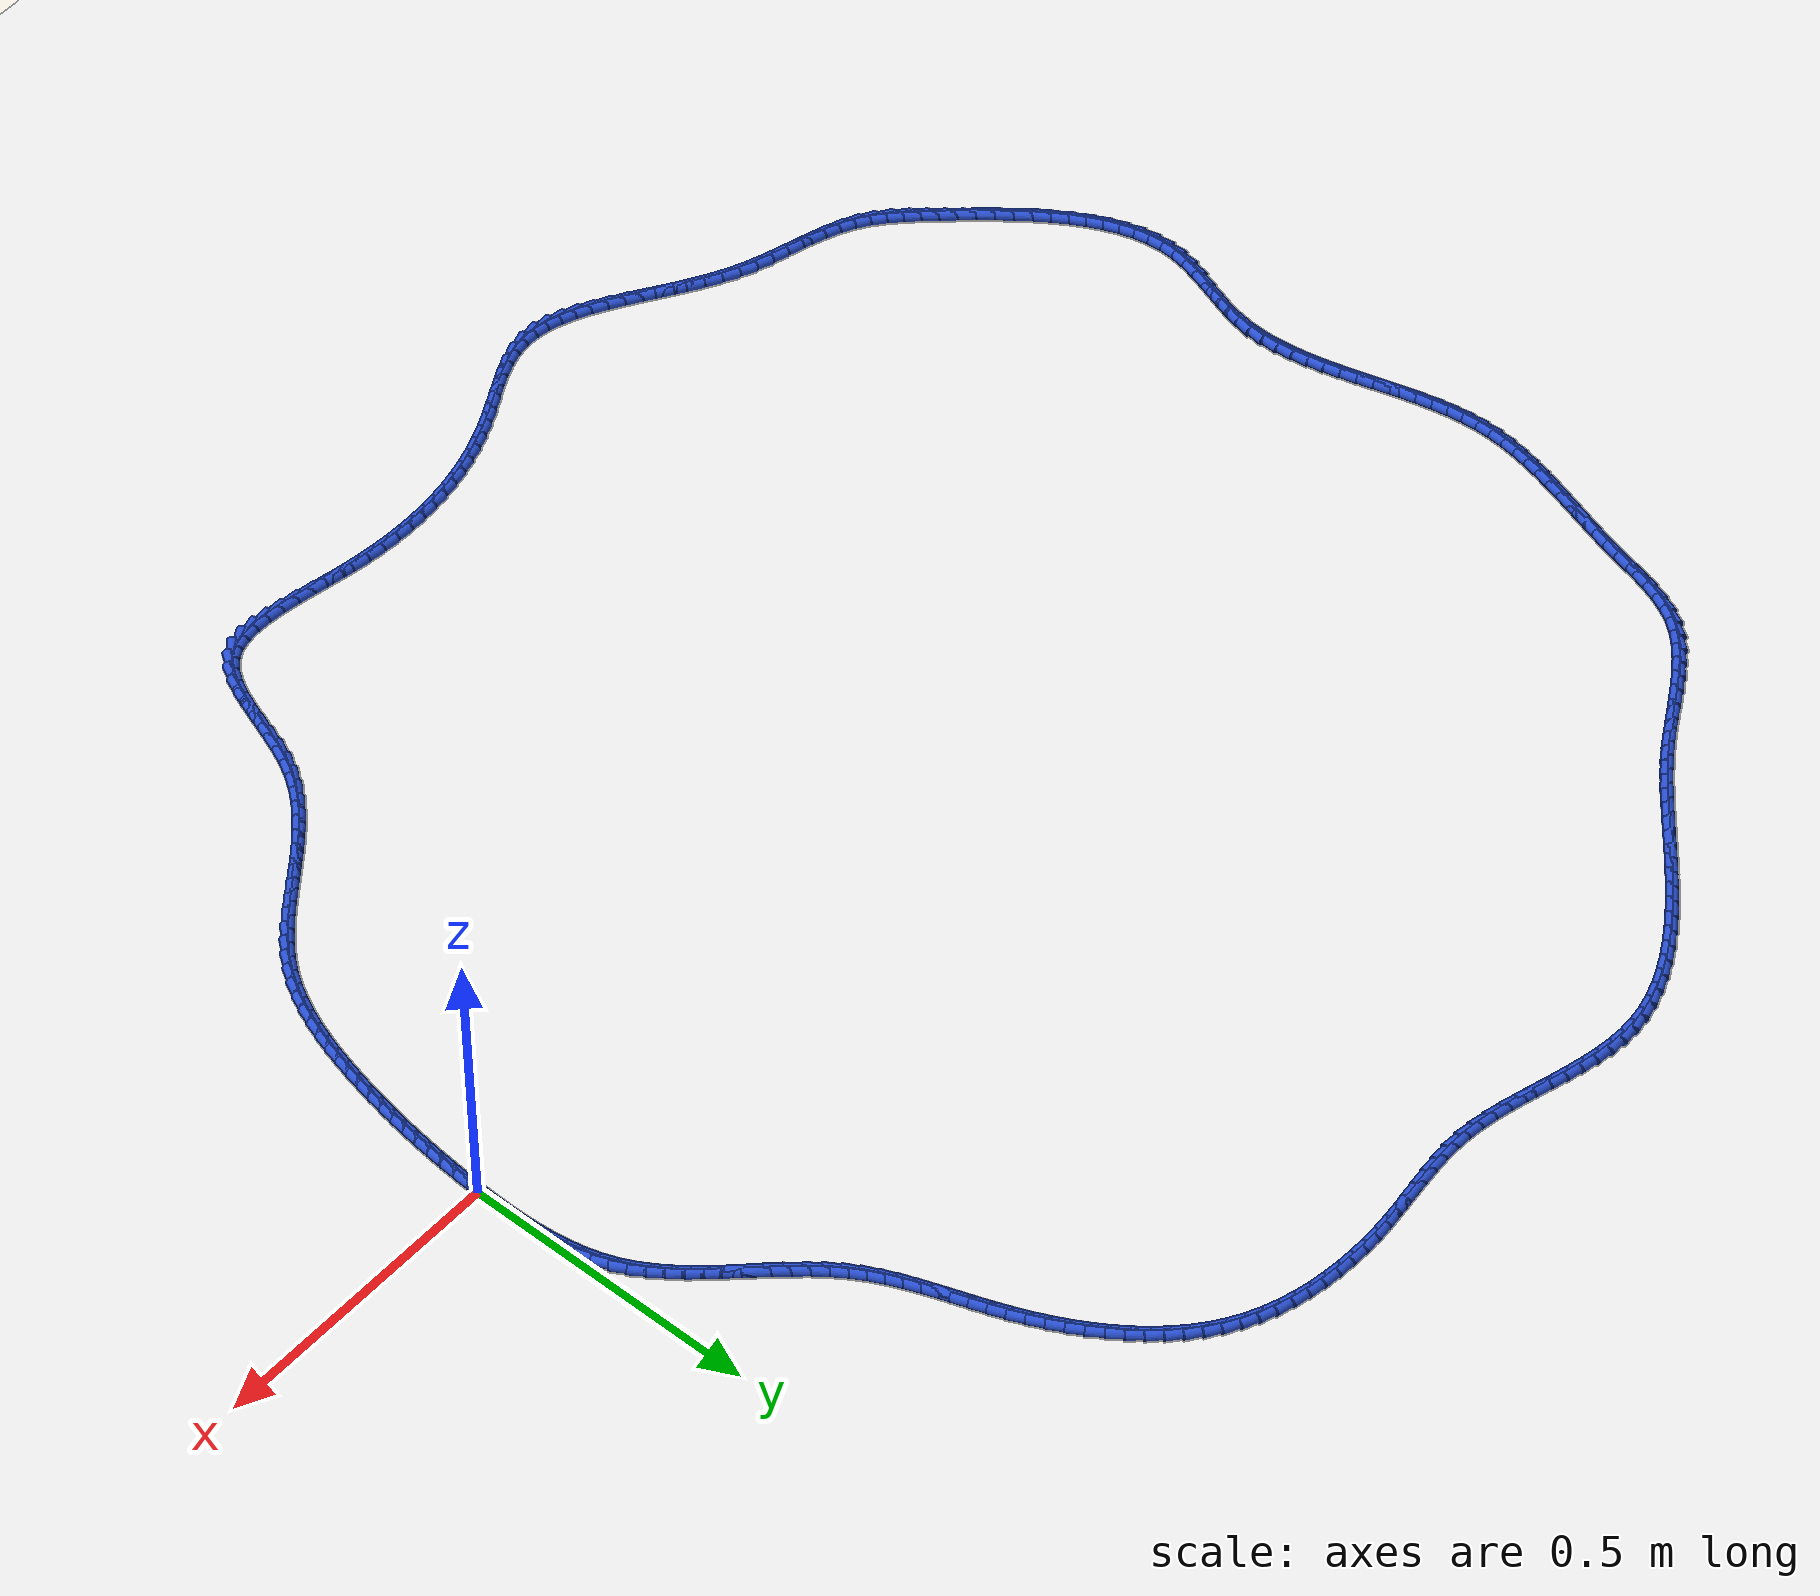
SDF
<sdf version="1.6">
 <world name="default">
  <light name="sun" type="directional">
   <pose>0 0 10 0 -0 0</pose>
   <diffuse>0.8 0.8 0.8 1</diffuse>
   <specular>0.2 0.2 0.2 1</specular>
   <attenuation>
    <range>1000</range>
    <constant>0.9</constant>
    <linear>0.01</linear>
    <quadratic>0.001</quadratic>
   </attenuation>
   <direction>-0.5 0.1 -0.9</direction>
  </light>
  <model name="ground_plane">
   <static>1</static>
   <link name="link">
    <collision name="collision">
     <geometry><plane><normal>0 0 1</normal><size>100 100</size></plane></geometry>
     <surface><friction><ode><mu>100</mu><mu2>50</mu2></ode></friction></surface>
    </collision>
    <visual name="visual">
     <cast_shadows>0</cast_shadows>
     <geometry><plane><normal>0 0 1</normal><size>100 100</size></plane></geometry>
     <material>
      <script><uri>file://media/materials/scripts/gazebo.material</uri><name>Gazebo/WhiteGlow</name></script>
     </material>
    </visual>
   </link>
  </model>
  <gravity>0 0 -9.8</gravity>
  <magnetic_field>6e-06 2.3e-05 -4.2e-05</magnetic_field>
  <atmosphere type="adiabatic"/>
  <physics name="default_physics" default="0" type="ode">
   <max_step_size>0.001</max_step_size>
   <real_time_factor>1</real_time_factor>
   <real_time_update_rate>1000</real_time_update_rate>
  </physics>
  <scene><ambient>0.4 0.4 0.4 1</ambient><background>0.7 0.7 0.7 1</background><shadows>1</shadows></scene>
  <spherical_coordinates>
   <surface_model>EARTH_WGS84</surface_model>
   <latitude_deg>0</latitude_deg>
   <longitude_deg>0</longitude_deg>
   <elevation>0</elevation>
   <heading_deg>0</heading_deg>
  </spherical_coordinates>
  <model name="line">
   <link name="link_0">
    <pose>5.44811591673966e-18 -4.85722573273506e-17 0.01 0 1.57 1.52936281463359</pose>
    <collision name="collision">
     <geometry><cylinder><radius>0.01</radius><length>0.08</length></cylinder></geometry>
    </collision>
    <visual name="visual">
     <material>
      <script><name>Gazebo/Blue</name><uri>file://media/materials/scripts/gazebo.material</uri></script>
     </material>
     <geometry><cylinder><radius>0.01</radius><length>0.08</length></cylinder></geometry>
    </visual>
   </link>
   <link name="link_1">
    <pose>0.0011541633781692302 0.02783985179669101 0.01 0 1.57 1.5510333189672778</pose>
    <collision name="collision">
     <geometry><cylinder><radius>0.01</radius><length>0.08</length></cylinder></geometry>
    </collision>
    <visual name="visual">
     <material>
      <script><name>Gazebo/Blue</name><uri>file://media/materials/scripts/gazebo.material</uri></script>
     </material>
     <geometry><cylinder><radius>0.01</radius><length>0.08</length></cylinder></geometry>
    </visual>
   </link>
   <link name="link_2">
    <pose>0.0017077863925077724 0.05584929954443413 0.01 0 1.57 -1.5615755259988313</pose>
    <collision name="collision">
     <geometry><cylinder><radius>0.01</radius><length>0.08</length></cylinder></geometry>
    </collision>
    <visual name="visual">
     <material>
      <script><name>Gazebo/Blue</name><uri>file://media/materials/scripts/gazebo.material</uri></script>
     </material>
     <geometry><cylinder><radius>0.01</radius><length>0.08</length></cylinder></geometry>
    </visual>
   </link>
   <link name="link_3">
    <pose>0.0014494072117952558 0.08386984392518775 0.01 0 1.57 -1.5248402342841438</pose>
    <collision name="collision">
     <geometry><cylinder><radius>0.01</radius><length>0.08</length></cylinder></geometry>
    </collision>
    <visual name="visual">
     <material>
      <script><name>Gazebo/Blue</name><uri>file://media/materials/scripts/gazebo.material</uri></script>
     </material>
     <geometry><cylinder><radius>0.01</radius><length>0.08</length></cylinder></geometry>
    </visual>
   </link>
   <link name="link_4">
    <pose>0.00016756400481130742 0.11174298562091044 0.01 0 1.57 -1.4797530624721642</pose>
    <collision name="collision">
     <geometry><cylinder><radius>0.01</radius><length>0.08</length></cylinder></geometry>
    </collision>
    <visual name="visual">
     <material>
      <script><name>Gazebo/Blue</name><uri>file://media/materials/scripts/gazebo.material</uri></script>
     </material>
     <geometry><cylinder><radius>0.01</radius><length>0.08</length></cylinder></geometry>
    </visual>
   </link>
   <link name="link_5">
    <pose>-0.0023492050596644453 0.13931022531356066 0.01 0 1.57 -1.425598742480633</pose>
    <collision name="collision">
     <geometry><cylinder><radius>0.01</radius><length>0.08</length></cylinder></geometry>
    </collision>
    <visual name="visual">
     <material>
      <script><name>Gazebo/Blue</name><uri>file://media/materials/scripts/gazebo.material</uri></script>
     </material>
     <geometry><cylinder><radius>0.01</radius><length>0.08</length></cylinder></geometry>
    </visual>
   </link>
   <link name="link_6">
    <pose>-0.006312361812852373 0.16641306368509692 0.01 0 1.57 -1.361627035891638</pose>
    <collision name="collision">
     <geometry><cylinder><radius>0.01</radius><length>0.08</length></cylinder></geometry>
    </collision>
    <visual name="visual">
     <material>
      <script><name>Gazebo/Blue</name><uri>file://media/materials/scripts/gazebo.material</uri></script>
     </material>
     <geometry><cylinder><radius>0.01</radius><length>0.08</length></cylinder></geometry>
    </visual>
   </link>
   <link name="link_7">
    <pose>-0.011933368085972852 0.1928930014174778 0.01 0 1.57 -1.2871847369622496</pose>
    <collision name="collision">
     <geometry><cylinder><radius>0.01</radius><length>0.08</length></cylinder></geometry>
    </collision>
    <visual name="visual">
     <material>
      <script><name>Gazebo/Blue</name><uri>file://media/materials/scripts/gazebo.material</uri></script>
     </material>
     <geometry><cylinder><radius>0.01</radius><length>0.08</length></cylinder></geometry>
    </visual>
   </link>
   <link name="link_8">
    <pose>-0.01942368571024626 0.21859153919266186 0.01 0 1.57 -1.2019158198015052</pose>
    <collision name="collision">
     <geometry><cylinder><radius>0.01</radius><length>0.08</length></cylinder></geometry>
    </collision>
    <visual name="visual">
     <material>
      <script><name>Gazebo/Blue</name><uri>file://media/materials/scripts/gazebo.material</uri></script>
     </material>
     <geometry><cylinder><radius>0.01</radius><length>0.08</length></cylinder></geometry>
    </visual>
   </link>
   <link name="link_9">
    <pose>-0.028994776516892966 0.2433501776926075 0.01 0 1.57 -1.107951390770927</pose>
    <collision name="collision">
     <geometry><cylinder><radius>0.01</radius><length>0.08</length></cylinder></geometry>
    </collision>
    <visual name="visual">
     <material>
      <script><name>Gazebo/Blue</name><uri>file://media/materials/scripts/gazebo.material</uri></script>
     </material>
     <geometry><cylinder><radius>0.01</radius><length>0.08</length></cylinder></geometry>
    </visual>
   </link>
   <link name="link_10">
    <pose>-0.04081411634225851 0.2670363689495163 0.01 0 1.57 -1.0215255866779043</pose>
    <collision name="collision">
     <geometry><cylinder><radius>0.01</radius><length>0.08</length></cylinder></geometry>
    </collision>
    <visual name="visual">
     <material>
      <script><name>Gazebo/Blue</name><uri>file://media/materials/scripts/gazebo.material</uri></script>
     </material>
     <geometry><cylinder><radius>0.01</radius><length>0.08</length></cylinder></geometry>
    </visual>
   </link>
   <link name="link_11">
    <pose>-0.054700741327095063 0.2897231413524448 0.01 0 1.57 -0.9507243869292543</pose>
    <collision name="collision">
     <geometry><cylinder><radius>0.01</radius><length>0.08</length></cylinder></geometry>
    </collision>
    <visual name="visual">
     <material>
      <script><name>Gazebo/Blue</name><uri>file://media/materials/scripts/gazebo.material</uri></script>
     </material>
     <geometry><cylinder><radius>0.01</radius><length>0.08</length></cylinder></geometry>
    </visual>
   </link>
   <link name="link_12">
    <pose>-0.07030788435505346 0.31158134575436575 0.01 0 1.57 -0.8955087621850788</pose>
    <collision name="collision">
     <geometry><cylinder><radius>0.01</radius><length>0.08</length></cylinder></geometry>
    </collision>
    <visual name="visual">
     <material>
      <script><name>Gazebo/Blue</name><uri>file://media/materials/scripts/gazebo.material</uri></script>
     </material>
     <geometry><cylinder><radius>0.01</radius><length>0.08</length></cylinder></geometry>
    </visual>
   </link>
   <link name="link_13">
    <pose>-0.08728776614763331 0.33278243017502257 0.01 0 1.57 -0.855288107946799</pose>
    <collision name="collision">
     <geometry><cylinder><radius>0.01</radius><length>0.08</length></cylinder></geometry>
    </collision>
    <visual name="visual">
     <material>
      <script><name>Gazebo/Blue</name><uri>file://media/materials/scripts/gazebo.material</uri></script>
     </material>
     <geometry><cylinder><radius>0.01</radius><length>0.08</length></cylinder></geometry>
    </visual>
   </link>
   <link name="link_14">
    <pose>-0.10529260742633428 0.3534978426341587 0.01 0 1.57 -0.8293571810454904</pose>
    <collision name="collision">
     <geometry><cylinder><radius>0.01</radius><length>0.08</length></cylinder></geometry>
    </collision>
    <visual name="visual">
     <material>
      <script><name>Gazebo/Blue</name><uri>file://media/materials/scripts/gazebo.material</uri></script>
     </material>
     <geometry><cylinder><radius>0.01</radius><length>0.08</length></cylinder></geometry>
    </visual>
   </link>
   <link name="link_15">
    <pose>-0.12397462891265597 0.37389903115151724 0.01 0 1.57 -0.8171419000854817</pose>
    <collision name="collision">
     <geometry><cylinder><radius>0.01</radius><length>0.08</length></cylinder></geometry>
    </collision>
    <visual name="visual">
     <material>
      <script><name>Gazebo/Blue</name><uri>file://media/materials/scripts/gazebo.material</uri></script>
     </material>
     <geometry><cylinder><radius>0.01</radius><length>0.08</length></cylinder></geometry>
    </visual>
   </link>
   <link name="link_16">
    <pose>-0.14298605132809802 0.39415744374684153 0.01 0 1.57 -0.8183301529669745</pose>
    <collision name="collision">
     <geometry><cylinder><radius>0.01</radius><length>0.08</length></cylinder></geometry>
    </collision>
    <visual name="visual">
     <material>
      <script><name>Gazebo/Blue</name><uri>file://media/materials/scripts/gazebo.material</uri></script>
     </material>
     <geometry><cylinder><radius>0.01</radius><length>0.08</length></cylinder></geometry>
    </visual>
   </link>
   <link name="link_17">
    <pose>-0.16197909539416017 0.414444528439875 0.01 0 1.57 -0.8329236838366222</pose>
    <collision name="collision">
     <geometry><cylinder><radius>0.01</radius><length>0.08</length></cylinder></geometry>
    </collision>
    <visual name="visual">
     <material>
      <script><name>Gazebo/Blue</name><uri>file://media/materials/scripts/gazebo.material</uri></script>
     </material>
     <geometry><cylinder><radius>0.01</radius><length>0.08</length></cylinder></geometry>
    </visual>
   </link>
   <link name="link_18">
    <pose>-0.1806059818323419 0.43493173325036066 0.01 0 1.57 -0.8612311229371086</pose>
    <collision name="collision">
     <geometry><cylinder><radius>0.01</radius><length>0.08</length></cylinder></geometry>
    </collision>
    <visual name="visual">
     <material>
      <script><name>Gazebo/Blue</name><uri>file://media/materials/scripts/gazebo.material</uri></script>
     </material>
     <geometry><cylinder><radius>0.01</radius><length>0.08</length></cylinder></geometry>
    </visual>
   </link>
   <link name="link_19">
    <pose>-0.19851893136414286 0.4557905061980421 0.01 0 1.57 -0.9038011137190111</pose>
    <collision name="collision">
     <geometry><cylinder><radius>0.01</radius><length>0.08</length></cylinder></geometry>
    </collision>
    <visual name="visual">
     <material>
      <script><name>Gazebo/Blue</name><uri>file://media/materials/scripts/gazebo.material</uri></script>
     </material>
     <geometry><cylinder><radius>0.01</radius><length>0.08</length></cylinder></geometry>
    </visual>
   </link>
   <link name="link_20">
    <pose>-0.21537016471106282 0.47719229530266244 0.01 0 1.57 -0.9612742751960943</pose>
    <collision name="collision">
     <geometry><cylinder><radius>0.01</radius><length>0.08</length></cylinder></geometry>
    </collision>
    <visual name="visual">
     <material>
      <script><name>Gazebo/Blue</name><uri>file://media/materials/scripts/gazebo.material</uri></script>
     </material>
     <geometry><cylinder><radius>0.01</radius><length>0.08</length></cylinder></geometry>
    </visual>
   </link>
   <link name="link_21">
    <pose>-0.23081190259460133 0.499308548583965 0.01 0 1.57 -1.0316155755889715</pose>
    <collision name="collision">
     <geometry><cylinder><radius>0.01</radius><length>0.08</length></cylinder></geometry>
    </collision>
    <visual name="visual">
     <material>
      <script><name>Gazebo/Blue</name><uri>file://media/materials/scripts/gazebo.material</uri></script>
     </material>
     <geometry><cylinder><radius>0.01</radius><length>0.08</length></cylinder></geometry>
    </visual>
   </link>
   <link name="link_22">
    <pose>-0.24455812770764399 0.5222833853581174 0.01 0 1.57 -1.0972253836234325</pose>
    <collision name="collision">
     <geometry><cylinder><radius>0.01</radius><length>0.08</length></cylinder></geometry>
    </collision>
    <visual name="visual">
     <material>
      <script><name>Gazebo/Blue</name><uri>file://media/materials/scripts/gazebo.material</uri></script>
     </material>
     <geometry><cylinder><radius>0.01</radius><length>0.08</length></cylinder></geometry>
    </visual>
   </link>
   <link name="link_23">
    <pose>-0.2567491406894277 0.5460722859370076 0.01 0 1.57 -1.1499652844287296</pose>
    <collision name="collision">
     <geometry><cylinder><radius>0.01</radius><length>0.08</length></cylinder></geometry>
    </collision>
    <visual name="visual">
     <material>
      <script><name>Gazebo/Blue</name><uri>file://media/materials/scripts/gazebo.material</uri></script>
     </material>
     <geometry><cylinder><radius>0.01</radius><length>0.08</length></cylinder></geometry>
    </visual>
   </link>
   <link name="link_24">
    <pose>-0.26770513062904844 0.5705511328150873 0.01 0 1.57 -1.1894629822158114</pose>
    <collision name="collision">
     <geometry><cylinder><radius>0.01</radius><length>0.08</length></cylinder></geometry>
    </collision>
    <visual name="visual">
     <material>
      <script><name>Gazebo/Blue</name><uri>file://media/materials/scripts/gazebo.material</uri></script>
     </material>
     <geometry><cylinder><radius>0.01</radius><length>0.08</length></cylinder></geometry>
    </visual>
   </link>
   <link name="link_25">
    <pose>-0.2777469211823199 0.5955955277009889 0.01 0 1.57 -1.2157689827839206</pose>
    <collision name="collision">
     <geometry><cylinder><radius>0.01</radius><length>0.08</length></cylinder></geometry>
    </collision>
    <visual name="visual">
     <material>
      <script><name>Gazebo/Blue</name><uri>file://media/materials/scripts/gazebo.material</uri></script>
     </material>
     <geometry><cylinder><radius>0.01</radius><length>0.08</length></cylinder></geometry>
    </visual>
   </link>
   <link name="link_26">
    <pose>-0.28719533600505603 0.6210810723033456 0.01 0 1.57 -1.2291218972281268</pose>
    <collision name="collision">
     <geometry><cylinder><radius>0.01</radius><length>0.08</length></cylinder></geometry>
    </collision>
    <visual name="visual">
     <material>
      <script><name>Gazebo/Blue</name><uri>file://media/materials/scripts/gazebo.material</uri></script>
     </material>
     <geometry><cylinder><radius>0.01</radius><length>0.08</length></cylinder></geometry>
    </visual>
   </link>
   <link name="link_27">
    <pose>-0.2963711987530705 0.64688336833079 0.01 0 1.57 -1.2298096322728906</pose>
    <collision name="collision">
     <geometry><cylinder><radius>0.01</radius><length>0.08</length></cylinder></geometry>
    </collision>
    <visual name="visual">
     <material>
      <script><name>Gazebo/Blue</name><uri>file://media/materials/scripts/gazebo.material</uri></script>
     </material>
     <geometry><cylinder><radius>0.01</radius><length>0.08</length></cylinder></geometry>
    </visual>
   </link>
   <link name="link_28">
    <pose>-0.3055953330821772 0.6728780174919547 0.01 0 1.57 -1.2181026734122422</pose>
    <collision name="collision">
     <geometry><cylinder><radius>0.01</radius><length>0.08</length></cylinder></geometry>
    </collision>
    <visual name="visual">
     <material>
      <script><name>Gazebo/Blue</name><uri>file://media/materials/scripts/gazebo.material</uri></script>
     </material>
     <geometry><cylinder><radius>0.01</radius><length>0.08</length></cylinder></geometry>
    </visual>
   </link>
   <link name="link_29">
    <pose>-0.31518856264818984 0.698940621495473 0.01 0 1.57 -1.1942646487385227</pose>
    <collision name="collision">
     <geometry><cylinder><radius>0.01</radius><length>0.08</length></cylinder></geometry>
    </collision>
    <visual name="visual">
     <material>
      <script><name>Gazebo/Blue</name><uri>file://media/materials/scripts/gazebo.material</uri></script>
     </material>
     <geometry><cylinder><radius>0.01</radius><length>0.08</length></cylinder></geometry>
    </visual>
   </link>
   <link name="link_30">
    <pose>-0.32547129347290776 0.7249467371017235 0.01 0 1.57 -1.161202773439375</pose>
    <collision name="collision">
     <geometry><cylinder><radius>0.01</radius><length>0.08</length></cylinder></geometry>
    </collision>
    <visual name="visual">
     <material>
      <script><name>Gazebo/Blue</name><uri>file://media/materials/scripts/gazebo.material</uri></script>
     </material>
     <geometry><cylinder><radius>0.01</radius><length>0.08</length></cylinder></geometry>
    </visual>
   </link>
   <link name="link_31">
    <pose>-0.33667929226755866 0.7507628116856874 0.01 0 1.57 -1.1247023041700943</pose>
    <collision name="collision">
     <geometry><cylinder><radius>0.01</radius><length>0.08</length></cylinder></geometry>
    </collision>
    <visual name="visual">
     <material>
      <script><name>Gazebo/Blue</name><uri>file://media/materials/scripts/gazebo.material</uri></script>
     </material>
     <geometry><cylinder><radius>0.01</radius><length>0.08</length></cylinder></geometry>
    </visual>
   </link>
   <link name="link_32">
    <pose>-0.3488613640812304 0.7762351706976317 0.01 0 1.57 -1.08517020894588</pose>
    <collision name="collision">
     <geometry><cylinder><radius>0.01</radius><length>0.08</length></cylinder></geometry>
    </collision>
    <visual name="visual">
     <material>
      <script><name>Gazebo/Blue</name><uri>file://media/materials/scripts/gazebo.material</uri></script>
     </material>
     <geometry><cylinder><radius>0.01</radius><length>0.08</length></cylinder></geometry>
    </visual>
   </link>
   <link name="link_33">
    <pose>-0.3620413056211553 0.8012074480415127 0.01 0 1.57 -1.042188933691912</pose>
    <collision name="collision">
     <geometry><cylinder><radius>0.01</radius><length>0.08</length></cylinder></geometry>
    </collision>
    <visual name="visual">
     <material>
      <script><name>Gazebo/Blue</name><uri>file://media/materials/scripts/gazebo.material</uri></script>
     </material>
     <geometry><cylinder><radius>0.01</radius><length>0.08</length></cylinder></geometry>
    </visual>
   </link>
   <link name="link_34">
    <pose>-0.3762429135945657 0.8255232776212864 0.01 0 1.57 -0.9953156247521674</pose>
    <collision name="collision">
     <geometry><cylinder><radius>0.01</radius><length>0.08</length></cylinder></geometry>
    </collision>
    <visual name="visual">
     <material>
      <script><name>Gazebo/Blue</name><uri>file://media/materials/scripts/gazebo.material</uri></script>
     </material>
     <geometry><cylinder><radius>0.01</radius><length>0.08</length></cylinder></geometry>
    </visual>
   </link>
   <link name="link_35">
    <pose>-0.3914899847086936 0.8490262933409088 0.01 0 1.57 -0.9440905224962252</pose>
    <collision name="collision">
     <geometry><cylinder><radius>0.01</radius><length>0.08</length></cylinder></geometry>
    </collision>
    <visual name="visual">
     <material>
      <script><name>Gazebo/Blue</name><uri>file://media/materials/scripts/gazebo.material</uri></script>
     </material>
     <geometry><cylinder><radius>0.01</radius><length>0.08</length></cylinder></geometry>
    </visual>
   </link>
   <link name="link_36">
    <pose>-0.4078063156707718 0.8715601291043363 0.01 0 1.57 -0.888053592743803</pose>
    <collision name="collision">
     <geometry><cylinder><radius>0.01</radius><length>0.08</length></cylinder></geometry>
    </collision>
    <visual name="visual">
     <material>
      <script><name>Gazebo/Blue</name><uri>file://media/materials/scripts/gazebo.material</uri></script>
     </material>
     <geometry><cylinder><radius>0.01</radius><length>0.08</length></cylinder></geometry>
    </visual>
   </link>
   <link name="link_37">
    <pose>-0.42521570318803215 0.8929684188155244 0.01 0 1.57 -0.8267724271265031</pose>
    <collision name="collision">
     <geometry><cylinder><radius>0.01</radius><length>0.08</length></cylinder></geometry>
    </collision>
    <visual name="visual">
     <material>
      <script><name>Gazebo/Blue</name><uri>file://media/materials/scripts/gazebo.material</uri></script>
     </material>
     <geometry><cylinder><radius>0.01</radius><length>0.08</length></cylinder></geometry>
    </visual>
   </link>
   <link name="link_38">
    <pose>-0.4437419439677074 0.9130947963784299 0.01 0 1.57 -0.7598844287268709</pose>
    <collision name="collision">
     <geometry><cylinder><radius>0.01</radius><length>0.08</length></cylinder></geometry>
    </collision>
    <visual name="visual">
     <material>
      <script><name>Gazebo/Blue</name><uri>file://media/materials/scripts/gazebo.material</uri></script>
     </material>
     <geometry><cylinder><radius>0.01</radius><length>0.08</length></cylinder></geometry>
    </visual>
   </link>
   <link name="link_39">
    <pose>-0.46340883471702954 0.9317828956970082 0.01 0 1.57 -0.6871550664892319</pose>
    <collision name="collision">
     <geometry><cylinder><radius>0.01</radius><length>0.08</length></cylinder></geometry>
    </collision>
    <visual name="visual">
     <material>
      <script><name>Gazebo/Blue</name><uri>file://media/materials/scripts/gazebo.material</uri></script>
     </material>
     <geometry><cylinder><radius>0.01</radius><length>0.08</length></cylinder></geometry>
    </visual>
   </link>
   <link name="link_40">
    <pose>-0.4842401721432311 0.9488763506752163 0.01 0 1.57 -0.6085506453058709</pose>
    <collision name="collision">
     <geometry><cylinder><radius>0.01</radius><length>0.08</length></cylinder></geometry>
    </collision>
    <visual name="visual">
     <material>
      <script><name>Gazebo/Blue</name><uri>file://media/materials/scripts/gazebo.material</uri></script>
     </material>
     <geometry><cylinder><radius>0.01</radius><length>0.08</length></cylinder></geometry>
    </visual>
   </link>
   <link name="link_41">
    <pose>-0.5062597529535444 0.9642187952170097 0.01 0 1.57 -0.524719948001382</pose>
    <collision name="collision">
     <geometry><cylinder><radius>0.01</radius><length>0.08</length></cylinder></geometry>
    </collision>
    <visual name="visual">
     <material>
      <script><name>Gazebo/Blue</name><uri>file://media/materials/scripts/gazebo.material</uri></script>
     </material>
     <geometry><cylinder><radius>0.01</radius><length>0.08</length></cylinder></geometry>
    </visual>
   </link>
   <link name="link_42">
    <pose>-0.529484953104132 0.977662612550448 0.01 0 1.57 -0.4420830428330021</pose>
    <collision name="collision">
     <geometry><cylinder><radius>0.01</radius><length>0.08</length></cylinder></geometry>
    </collision>
    <visual name="visual">
     <material>
      <script><name>Gazebo/Blue</name><uri>file://media/materials/scripts/gazebo.material</uri></script>
     </material>
     <geometry><cylinder><radius>0.01</radius><length>0.08</length></cylinder></geometry>
    </visual>
   </link>
   <link name="link_43">
    <pose>-0.553838139457276 0.9891896513424778 0.01 0 1.57 -0.36539689269795744</pose>
    <collision name="collision">
     <geometry><cylinder><radius>0.01</radius><length>0.08</length></cylinder></geometry>
    </collision>
    <visual name="visual">
     <material>
      <script><name>Gazebo/Blue</name><uri>file://media/materials/scripts/gazebo.material</uri></script>
     </material>
     <geometry><cylinder><radius>0.01</radius><length>0.08</length></cylinder></geometry>
    </visual>
   </link>
   <link name="link_44">
    <pose>-0.5791690812609851 0.99888068639027 0.01 0 1.57 -0.2946567010735489</pose>
    <collision name="collision">
     <geometry><cylinder><radius>0.01</radius><length>0.08</length></cylinder></geometry>
    </collision>
    <visual name="visual">
     <material>
      <script><name>Gazebo/Blue</name><uri>file://media/materials/scripts/gazebo.material</uri></script>
     </material>
     <geometry><cylinder><radius>0.01</radius><length>0.08</length></cylinder></geometry>
    </visual>
   </link>
   <link name="link_45">
    <pose>-0.6053257112593284 1.0068189950281625 0.01 0 1.57 -0.22953121865876785</pose>
    <collision name="collision">
     <geometry><cylinder><radius>0.01</radius><length>0.08</length></cylinder></geometry>
    </collision>
    <visual name="visual">
     <material>
      <script><name>Gazebo/Blue</name><uri>file://media/materials/scripts/gazebo.material</uri></script>
     </material>
     <geometry><cylinder><radius>0.01</radius><length>0.08</length></cylinder></geometry>
    </visual>
   </link>
   <link name="link_46">
    <pose>-0.6321559621963749 1.013087854590494 0.01 0 1.57 -0.16955831056923235</pose>
    <collision name="collision">
     <geometry><cylinder><radius>0.01</radius><length>0.08</length></cylinder></geometry>
    </collision>
    <visual name="visual">
     <material>
      <script><name>Gazebo/Blue</name><uri>file://media/materials/scripts/gazebo.material</uri></script>
     </material>
     <geometry><cylinder><radius>0.01</radius><length>0.08</length></cylinder></geometry>
    </visual>
   </link>
   <link name="link_47">
    <pose>-0.659507766816193 1.017770542411602 0.01 0 1.57 -0.11420667659082309</pose>
    <collision name="collision">
     <geometry><cylinder><radius>0.01</radius><length>0.08</length></cylinder></geometry>
    </collision>
    <visual name="visual">
     <material>
      <script><name>Gazebo/Blue</name><uri>file://media/materials/scripts/gazebo.material</uri></script>
     </material>
     <geometry><cylinder><radius>0.01</radius><length>0.08</length></cylinder></geometry>
    </visual>
   </link>
   <link name="link_48">
    <pose>-0.687229057862852 1.0209503358258252 0.01 0 1.57 -0.06291818933645081</pose>
    <collision name="collision">
     <geometry><cylinder><radius>0.01</radius><length>0.08</length></cylinder></geometry>
    </collision>
    <visual name="visual">
     <material>
      <script><name>Gazebo/Blue</name><uri>file://media/materials/scripts/gazebo.material</uri></script>
     </material>
     <geometry><cylinder><radius>0.01</radius><length>0.08</length></cylinder></geometry>
    </visual>
   </link>
   <link name="link_49">
    <pose>-0.7151677680804205 1.0227105121675015 0.01 0 1.57 -0.015133670399451406</pose>
    <collision name="collision">
     <geometry><cylinder><radius>0.01</radius><length>0.08</length></cylinder></geometry>
    </collision>
    <visual name="visual">
     <material>
      <script><name>Gazebo/Blue</name><uri>file://media/materials/scripts/gazebo.material</uri></script>
     </material>
     <geometry><cylinder><radius>0.01</radius><length>0.08</length></cylinder></geometry>
    </visual>
   </link>
   <link name="link_50">
    <pose>-0.7431718302129673 1.023134348770969 0.01 0 1.57 0.029694156501853492</pose>
    <collision name="collision">
     <geometry><cylinder><radius>0.01</radius><length>0.08</length></cylinder></geometry>
    </collision>
    <visual name="visual">
     <material>
      <script><name>Gazebo/Blue</name><uri>file://media/materials/scripts/gazebo.material</uri></script>
     </material>
     <geometry><cylinder><radius>0.01</radius><length>0.08</length></cylinder></geometry>
    </visual>
   </link>
   <link name="link_51">
    <pose>-0.7710891770045614 1.022305122970566 0.01 0 1.57 0.07107071263932781</pose>
    <collision name="collision">
     <geometry><cylinder><radius>0.01</radius><length>0.08</length></cylinder></geometry>
    </collision>
    <visual name="visual">
     <material>
      <script><name>Gazebo/Blue</name><uri>file://media/materials/scripts/gazebo.material</uri></script>
     </material>
     <geometry><cylinder><radius>0.01</radius><length>0.08</length></cylinder></geometry>
    </visual>
   </link>
   <link name="link_52">
    <pose>-0.798783662838398 1.0203335354813368 0.01 0 1.57 0.10146768350063638</pose>
    <collision name="collision">
     <geometry><cylinder><radius>0.01</radius><length>0.08</length></cylinder></geometry>
    </collision>
    <visual name="visual">
     <material>
      <script><name>Gazebo/Blue</name><uri>file://media/materials/scripts/gazebo.material</uri></script>
     </material>
     <geometry><cylinder><radius>0.01</radius><length>0.08</length></cylinder></geometry>
    </visual>
   </link>
   <link name="link_53">
    <pose>-0.826239754249707 1.0175380290062432 0.01 0 1.57 0.11707617096821583</pose>
    <collision name="collision">
     <geometry><cylinder><radius>0.01</radius><length>0.08</length></cylinder></geometry>
    </collision>
    <visual name="visual">
     <material>
      <script><name>Gazebo/Blue</name><uri>file://media/materials/scripts/gazebo.material</uri></script>
     </material>
     <geometry><cylinder><radius>0.01</radius><length>0.08</length></cylinder></geometry>
    </visual>
   </link>
   <link name="link_54">
    <pose>-0.8534971492730531 1.01433217680743 0.01 0 1.57 0.11762012950102028</pose>
    <collision name="collision">
     <geometry><cylinder><radius>0.01</radius><length>0.08</length></cylinder></geometry>
    </collision>
    <visual name="visual">
     <material>
      <script><name>Gazebo/Blue</name><uri>file://media/materials/scripts/gazebo.material</uri></script>
     </material>
     <geometry><cylinder><radius>0.01</radius><length>0.08</length></cylinder></geometry>
    </visual>
   </link>
   <link name="link_55">
    <pose>-0.8805958326123193 1.011130045905367 0.01 0 1.57 0.10283636188877936</pose>
    <collision name="collision">
     <geometry><cylinder><radius>0.01</radius><length>0.08</length></cylinder></geometry>
    </collision>
    <visual name="visual">
     <material>
      <script><name>Gazebo/Blue</name><uri>file://media/materials/scripts/gazebo.material</uri></script>
     </material>
     <geometry><cylinder><radius>0.01</radius><length>0.08</length></cylinder></geometry>
    </visual>
   </link>
   <link name="link_56">
    <pose>-0.9075757889713887 1.0083457033205239 0.01 0 1.57 0.07245284814458858</pose>
    <collision name="collision">
     <geometry><cylinder><radius>0.01</radius><length>0.08</length></cylinder></geometry>
    </collision>
    <visual name="visual">
     <material>
      <script><name>Gazebo/Blue</name><uri>file://media/materials/scripts/gazebo.material</uri></script>
     </material>
     <geometry><cylinder><radius>0.01</radius><length>0.08</length></cylinder></geometry>
    </visual>
   </link>
   <link name="link_57">
    <pose>-0.9344770030541438 1.0063932160733704 0.01 0 1.57 0.026296999696374317</pose>
    <collision name="collision">
     <geometry><cylinder><radius>0.01</radius><length>0.08</length></cylinder></geometry>
    </collision>
    <visual name="visual">
     <material>
      <script><name>Gazebo/Blue</name><uri>file://media/materials/scripts/gazebo.material</uri></script>
     </material>
     <geometry><cylinder><radius>0.01</radius><length>0.08</length></cylinder></geometry>
    </visual>
   </link>
   <link name="link_58">
    <pose>-0.9613394595644681 1.0056866511843763 0.01 0 1.57 -0.03547631387141171</pose>
    <collision name="collision">
     <geometry><cylinder><radius>0.01</radius><length>0.08</length></cylinder></geometry>
    </collision>
    <visual name="visual">
     <material>
      <script><name>Gazebo/Blue</name><uri>file://media/materials/scripts/gazebo.material</uri></script>
     </material>
     <geometry><cylinder><radius>0.01</radius><length>0.08</length></cylinder></geometry>
    </visual>
   </link>
   <link name="link_59">
    <pose>-0.9882031432062449 1.006640075674012 0.01 0 1.57 -0.10895167903751317</pose>
    <collision name="collision">
     <geometry><cylinder><radius>0.01</radius><length>0.08</length></cylinder></geometry>
    </collision>
    <visual name="visual">
     <material>
      <script><name>Gazebo/Blue</name><uri>file://media/materials/scripts/gazebo.material</uri></script>
     </material>
     <geometry><cylinder><radius>0.01</radius><length>0.08</length></cylinder></geometry>
    </visual>
   </link>
   <link name="link_60">
    <pose>-1.0151019509358852 1.0095823974096465 0.01 0 1.57 -0.17348990089580207</pose>
    <collision name="collision">
     <geometry><cylinder><radius>0.01</radius><length>0.08</length></cylinder></geometry>
    </collision>
    <visual name="visual">
     <material>
      <script><name>Gazebo/Blue</name><uri>file://media/materials/scripts/gazebo.material</uri></script>
     </material>
     <geometry><cylinder><radius>0.01</radius><length>0.08</length></cylinder></geometry>
    </visual>
   </link>
   <link name="link_61">
    <pose>-1.0420311237832824 1.0143017814009399 0.01 0 1.57 -0.2217252626227899</pose>
    <collision name="collision">
     <geometry><cylinder><radius>0.01</radius><length>0.08</length></cylinder></geometry>
    </collision>
    <visual name="visual">
     <material>
      <script><name>Gazebo/Blue</name><uri>file://media/materials/scripts/gazebo.material</uri></script>
     </material>
     <geometry><cylinder><radius>0.01</radius><length>0.08</length></cylinder></geometry>
    </visual>
   </link>
   <link name="link_62">
    <pose>-1.0689707790428966 1.0203748325514117 0.01 0 1.57 -0.2544019854768257</pose>
    <collision name="collision">
     <geometry><cylinder><radius>0.01</radius><length>0.08</length></cylinder></geometry>
    </collision>
    <visual name="visual">
     <material>
      <script><name>Gazebo/Blue</name><uri>file://media/materials/scripts/gazebo.material</uri></script>
     </material>
     <geometry><cylinder><radius>0.01</radius><length>0.08</length></cylinder></geometry>
    </visual>
   </link>
   <link name="link_63">
    <pose>-1.095900998937153 1.0273776651554178 0.01 0 1.57 -0.27219795656285345</pose>
    <collision name="collision">
     <geometry><cylinder><radius>0.01</radius><length>0.08</length></cylinder></geometry>
    </collision>
    <visual name="visual">
     <material>
      <script><name>Gazebo/Blue</name><uri>file://media/materials/scripts/gazebo.material</uri></script>
     </material>
     <geometry><cylinder><radius>0.01</radius><length>0.08</length></cylinder></geometry>
    </visual>
   </link>
   <link name="link_64">
    <pose>-1.1228018656884784 1.0348863935073147 0.01 0 1.57 -0.27550348878206676</pose>
    <collision name="collision">
     <geometry><cylinder><radius>0.01</radius><length>0.08</length></cylinder></geometry>
    </collision>
    <visual name="visual">
     <material>
      <script><name>Gazebo/Blue</name><uri>file://media/materials/scripts/gazebo.material</uri></script>
     </material>
     <geometry><cylinder><radius>0.01</radius><length>0.08</length></cylinder></geometry>
    </visual>
   </link>
   <link name="link_65">
    <pose>-1.1496534615192986 1.042477131901458 0.01 0 1.57 -0.26432467537369103</pose>
    <collision name="collision">
     <geometry><cylinder><radius>0.01</radius><length>0.08</length></cylinder></geometry>
    </collision>
    <visual name="visual">
     <material>
      <script><name>Gazebo/Blue</name><uri>file://media/materials/scripts/gazebo.material</uri></script>
     </material>
     <geometry><cylinder><radius>0.01</radius><length>0.08</length></cylinder></geometry>
    </visual>
   </link>
   <link name="link_66">
    <pose>-1.1764358686520393 1.049725994632204 0.01 0 1.57 -0.23826041667342834</pose>
    <collision name="collision">
     <geometry><cylinder><radius>0.01</radius><length>0.08</length></cylinder></geometry>
    </collision>
    <visual name="visual">
     <material>
      <script><name>Gazebo/Blue</name><uri>file://media/materials/scripts/gazebo.material</uri></script>
     </material>
     <geometry><cylinder><radius>0.01</radius><length>0.08</length></cylinder></geometry>
    </visual>
   </link>
   <link name="link_67">
    <pose>-1.2031291693091266 1.0562090959939079 0.01 0 1.57 -0.19654901584674972</pose>
    <collision name="collision">
     <geometry><cylinder><radius>0.01</radius><length>0.08</length></cylinder></geometry>
    </collision>
    <visual name="visual">
     <material>
      <script><name>Gazebo/Blue</name><uri>file://media/materials/scripts/gazebo.material</uri></script>
     </material>
     <geometry><cylinder><radius>0.01</radius><length>0.08</length></cylinder></geometry>
    </visual>
   </link>
   <link name="link_68">
    <pose>-1.2297134457129866 1.061502550280926 0.01 0 1.57 -0.1382125585753608</pose>
    <collision name="collision">
     <geometry><cylinder><radius>0.01</radius><length>0.08</length></cylinder></geometry>
    </collision>
    <visual name="visual">
     <material>
      <script><name>Gazebo/Blue</name><uri>file://media/materials/scripts/gazebo.material</uri></script>
     </material>
     <geometry><cylinder><radius>0.01</radius><length>0.08</length></cylinder></geometry>
    </visual>
   </link>
   <link name="link_69">
    <pose>-1.2561687800860453 1.0651824717876144 0.01 0 1.57 -0.06235626952176293</pose>
    <collision name="collision">
     <geometry><cylinder><radius>0.01</radius><length>0.08</length></cylinder></geometry>
    </collision>
    <visual name="visual">
     <material>
      <script><name>Gazebo/Blue</name><uri>file://media/materials/scripts/gazebo.material</uri></script>
     </material>
     <geometry><cylinder><radius>0.01</radius><length>0.08</length></cylinder></geometry>
    </visual>
   </link>
   <link name="link_70">
    <pose>-1.282475254650729 1.066824974808329 0.01 0 1.57 0.0313038524707301</pose>
    <collision name="collision">
     <geometry><cylinder><radius>0.01</radius><length>0.08</length></cylinder></geometry>
    </collision>
    <visual name="visual">
     <material>
      <script><name>Gazebo/Blue</name><uri>file://media/materials/scripts/gazebo.material</uri></script>
     </material>
     <geometry><cylinder><radius>0.01</radius><length>0.08</length></cylinder></geometry>
    </visual>
   </link>
   <link name="link_71">
    <pose>-1.3086129426936903 1.0660064971098333 0.01 0 1.57 0.1354745483552707</pose>
    <collision name="collision">
     <geometry><cylinder><radius>0.01</radius><length>0.08</length></cylinder></geometry>
    </collision>
    <visual name="visual">
     <material>
      <script><name>Gazebo/Blue</name><uri>file://media/materials/scripts/gazebo.material</uri></script>
     </material>
     <geometry><cylinder><radius>0.01</radius><length>0.08</length></cylinder></geometry>
    </visual>
   </link>
   <link name="link_72">
    <pose>-1.3345573164568127 1.0624700329481653 0.01 0 1.57 0.2319395188891165</pose>
    <collision name="collision">
     <geometry><cylinder><radius>0.01</radius><length>0.08</length></cylinder></geometry>
    </collision>
    <visual name="visual">
     <material>
      <script><name>Gazebo/Blue</name><uri>file://media/materials/scripts/gazebo.material</uri></script>
     </material>
     <geometry><cylinder><radius>0.01</radius><length>0.08</length></cylinder></geometry>
    </visual>
   </link>
   <link name="link_73">
    <pose>-1.3602717497239893 1.0563965372578765 0.01 0 1.57 0.317375319440781</pose>
    <collision name="collision">
     <geometry><cylinder><radius>0.01</radius><length>0.08</length></cylinder></geometry>
    </collision>
    <visual name="visual">
     <material>
      <script><name>Gazebo/Blue</name><uri>file://media/materials/scripts/gazebo.material</uri></script>
     </material>
     <geometry><cylinder><radius>0.01</radius><length>0.08</length></cylinder></geometry>
    </visual>
   </link>
   <link name="link_74">
    <pose>-1.385717651409943 1.0480380926689317 0.01 0 1.57 0.3919684377687647</pose>
    <collision name="collision">
     <geometry><cylinder><radius>0.01</radius><length>0.08</length></cylinder></geometry>
    </collision>
    <visual name="visual">
     <material>
      <script><name>Gazebo/Blue</name><uri>file://media/materials/scripts/gazebo.material</uri></script>
     </material>
     <geometry><cylinder><radius>0.01</radius><length>0.08</length></cylinder></geometry>
    </visual>
   </link>
   <link name="link_75">
    <pose>-1.4108564304293956 1.037646781811295 0.01 0 1.57 0.456379453697414</pose>
    <collision name="collision">
     <geometry><cylinder><radius>0.01</radius><length>0.08</length></cylinder></geometry>
    </collision>
    <visual name="visual">
     <material>
      <script><name>Gazebo/Blue</name><uri>file://media/materials/scripts/gazebo.material</uri></script>
     </material>
     <geometry><cylinder><radius>0.01</radius><length>0.08</length></cylinder></geometry>
    </visual>
   </link>
   <link name="link_76">
    <pose>-1.4356494956970693 1.0254746873149307 0.01 0 1.57 0.5114823510553568</pose>
    <collision name="collision">
     <geometry><cylinder><radius>0.01</radius><length>0.08</length></cylinder></geometry>
    </collision>
    <visual name="visual">
     <material>
      <script><name>Gazebo/Blue</name><uri>file://media/materials/scripts/gazebo.material</uri></script>
     </material>
     <geometry><cylinder><radius>0.01</radius><length>0.08</length></cylinder></geometry>
    </visual>
   </link>
   <link name="link_77">
    <pose>-1.4600582561276858 1.0117738918098034 0.01 0 1.57 0.5581869383137341</pose>
    <collision name="collision">
     <geometry><cylinder><radius>0.01</radius><length>0.08</length></cylinder></geometry>
    </collision>
    <visual name="visual">
     <material>
      <script><name>Gazebo/Blue</name><uri>file://media/materials/scripts/gazebo.material</uri></script>
     </material>
     <geometry><cylinder><radius>0.01</radius><length>0.08</length></cylinder></geometry>
    </visual>
   </link>
   <link name="link_78">
    <pose>-1.4840441206359687 0.9967964779258773 0.01 0 1.57 0.5973328220931737</pose>
    <collision name="collision">
     <geometry><cylinder><radius>0.01</radius><length>0.08</length></cylinder></geometry>
    </collision>
    <visual name="visual">
     <material>
      <script><name>Gazebo/Blue</name><uri>file://media/materials/scripts/gazebo.material</uri></script>
     </material>
     <geometry><cylinder><radius>0.01</radius><length>0.08</length></cylinder></geometry>
    </visual>
   </link>
   <link name="link_79">
    <pose>-1.50756849813664 0.9807945282931176 0.01 0 1.57 0.6296325864887741</pose>
    <collision name="collision">
     <geometry><cylinder><radius>0.01</radius><length>0.08</length></cylinder></geometry>
    </collision>
    <visual name="visual">
     <material>
      <script><name>Gazebo/Blue</name><uri>file://media/materials/scripts/gazebo.material</uri></script>
     </material>
     <geometry><cylinder><radius>0.01</radius><length>0.08</length></cylinder></geometry>
    </visual>
   </link>
   <link name="link_80">
    <pose>-1.5305927975444213 0.9640201255414883 0.01 0 1.57 0.6556435045871363</pose>
    <collision name="collision">
     <geometry><cylinder><radius>0.01</radius><length>0.08</length></cylinder></geometry>
    </collision>
    <visual name="visual">
     <material>
      <script><name>Gazebo/Blue</name><uri>file://media/materials/scripts/gazebo.material</uri></script>
     </material>
     <geometry><cylinder><radius>0.01</radius><length>0.08</length></cylinder></geometry>
    </visual>
   </link>
   <link name="link_81">
    <pose>-1.553078427774035 0.9467253523009532 0.01 0 1.57 0.675752611051536</pose>
    <collision name="collision">
     <geometry><cylinder><radius>0.01</radius><length>0.08</length></cylinder></geometry>
    </collision>
    <visual name="visual">
     <material>
      <script><name>Gazebo/Blue</name><uri>file://media/materials/scripts/gazebo.material</uri></script>
     </material>
     <geometry><cylinder><radius>0.01</radius><length>0.08</length></cylinder></geometry>
    </visual>
   </link>
   <link name="link_82">
    <pose>-1.5749870564986381 0.9291620704523046 0.01 0 1.57 0.6902067509968366</pose>
    <collision name="collision">
     <geometry><cylinder><radius>0.01</radius><length>0.08</length></cylinder></geometry>
    </collision>
    <visual name="visual">
     <material>
      <script><name>Gazebo/Blue</name><uri>file://media/materials/scripts/gazebo.material</uri></script>
     </material>
     <geometry><cylinder><radius>0.01</radius><length>0.08</length></cylinder></geometry>
    </visual>
   </link>
   <link name="link_83">
    <pose>-1.5963386552855237 0.9115324022937841 0.01 0 1.57 0.6989801272872999</pose>
    <collision name="collision">
     <geometry><cylinder><radius>0.01</radius><length>0.08</length></cylinder></geometry>
    </collision>
    <visual name="visual">
     <material>
      <script><name>Gazebo/Blue</name><uri>file://media/materials/scripts/gazebo.material</uri></script>
     </material>
     <geometry><cylinder><radius>0.01</radius><length>0.08</length></cylinder></geometry>
    </visual>
   </link>
   <link name="link_84">
    <pose>-1.6172850144167623 0.8939260143787491 0.01 0 1.57 0.7018116798147105</pose>
    <collision name="collision">
     <geometry><cylinder><radius>0.01</radius><length>0.08</length></cylinder></geometry>
    </collision>
    <visual name="visual">
     <material>
      <script><name>Gazebo/Blue</name><uri>file://media/materials/scripts/gazebo.material</uri></script>
     </material>
     <geometry><cylinder><radius>0.01</radius><length>0.08</length></cylinder></geometry>
    </visual>
   </link>
   <link name="link_85">
    <pose>-1.637996032143512 0.8764171251873822 0.01 0 1.57 0.6985146719682829</pose>
    <collision name="collision">
     <geometry><cylinder><radius>0.01</radius><length>0.08</length></cylinder></geometry>
    </collision>
    <visual name="visual">
     <material>
      <script><name>Gazebo/Blue</name><uri>file://media/materials/scripts/gazebo.material</uri></script>
     </material>
     <geometry><cylinder><radius>0.01</radius><length>0.08</length></cylinder></geometry>
    </visual>
   </link>
   <link name="link_86">
    <pose>-1.658641606716928 0.859079953199866 0.01 0 1.57 0.6890098601482795</pose>
    <collision name="collision">
     <geometry><cylinder><radius>0.01</radius><length>0.08</length></cylinder></geometry>
    </collision>
    <visual name="visual">
     <material>
      <script><name>Gazebo/Blue</name><uri>file://media/materials/scripts/gazebo.material</uri></script>
     </material>
     <geometry><cylinder><radius>0.01</radius><length>0.08</length></cylinder></geometry>
    </visual>
   </link>
   <link name="link_87">
    <pose>-1.6793916363881651 0.841988716896382 0.01 0 1.57 0.673334946599743</pose>
    <collision name="collision">
     <geometry><cylinder><radius>0.01</radius><length>0.08</length></cylinder></geometry>
    </collision>
    <visual name="visual">
     <material>
      <script><name>Gazebo/Blue</name><uri>file://media/materials/scripts/gazebo.material</uri></script>
     </material>
     <geometry><cylinder><radius>0.01</radius><length>0.08</length></cylinder></geometry>
    </visual>
   </link>
   <link name="link_88">
    <pose>-1.7004160194083808 0.8252176347571134 0.01 0 1.57 0.6516557136667185</pose>
    <collision name="collision">
     <geometry><cylinder><radius>0.01</radius><length>0.08</length></cylinder></geometry>
    </collision>
    <visual name="visual">
     <material>
      <script><name>Gazebo/Blue</name><uri>file://media/materials/scripts/gazebo.material</uri></script>
     </material>
     <geometry><cylinder><radius>0.01</radius><length>0.08</length></cylinder></geometry>
    </visual>
   </link>
   <link name="link_89">
    <pose>-1.7218846540287305 0.8088409252622418 0.01 0 1.57 0.6242769112387478</pose>
    <collision name="collision">
     <geometry><cylinder><radius>0.01</radius><length>0.08</length></cylinder></geometry>
    </collision>
    <visual name="visual">
     <material>
      <script><name>Gazebo/Blue</name><uri>file://media/materials/scripts/gazebo.material</uri></script>
     </material>
     <geometry><cylinder><radius>0.01</radius><length>0.08</length></cylinder></geometry>
    </visual>
   </link>
   <link name="link_90">
    <pose>-1.7439674385003705 0.7929328068919499 0.01 0 1.57 0.5916496264576836</pose>
    <collision name="collision">
     <geometry><cylinder><radius>0.01</radius><length>0.08</length></cylinder></geometry>
    </collision>
    <visual name="visual">
     <material>
      <script><name>Gazebo/Blue</name><uri>file://media/materials/scripts/gazebo.material</uri></script>
     </material>
     <geometry><cylinder><radius>0.01</radius><length>0.08</length></cylinder></geometry>
    </visual>
   </link>
   <link name="link_91">
    <pose>-1.7668342702152673 0.7775674975974827 0.01 0 1.57 0.5582480831863609</pose>
    <collision name="collision">
     <geometry><cylinder><radius>0.01</radius><length>0.08</length></cylinder></geometry>
    </collision>
    <visual name="visual">
     <material>
      <script><name>Gazebo/Blue</name><uri>file://media/materials/scripts/gazebo.material</uri></script>
     </material>
     <geometry><cylinder><radius>0.01</radius><length>0.08</length></cylinder></geometry>
    </visual>
   </link>
   <link name="link_92">
    <pose>-1.7905517750524946 0.7627556389257502 0.01 0 1.57 0.5385629107055593</pose>
    <collision name="collision">
     <geometry><cylinder><radius>0.01</radius><length>0.08</length></cylinder></geometry>
    </collision>
    <visual name="visual">
     <material>
      <script><name>Gazebo/Blue</name><uri>file://media/materials/scripts/gazebo.material</uri></script>
     </material>
     <geometry><cylinder><radius>0.01</radius><length>0.08</length></cylinder></geometry>
    </visual>
   </link>
   <link name="link_93">
    <pose>-1.8147983319588759 0.7482688583601029 0.01 0 1.57 0.5352295806216182</pose>
    <collision name="collision">
     <geometry><cylinder><radius>0.01</radius><length>0.08</length></cylinder></geometry>
    </collision>
    <visual name="visual">
     <material>
      <script><name>Gazebo/Blue</name><uri>file://media/materials/scripts/gazebo.material</uri></script>
     </material>
     <geometry><cylinder><radius>0.01</radius><length>0.08</length></cylinder></geometry>
    </visual>
   </link>
   <link name="link_94">
    <pose>-1.8391610987646003 0.7338226254906587 0.01 0 1.57 0.5480389650795627</pose>
    <collision name="collision">
     <geometry><cylinder><radius>0.01</radius><length>0.08</length></cylinder></geometry>
    </collision>
    <visual name="visual">
     <material>
      <script><name>Gazebo/Blue</name><uri>file://media/materials/scripts/gazebo.material</uri></script>
     </material>
     <geometry><cylinder><radius>0.01</radius><length>0.08</length></cylinder></geometry>
    </visual>
   </link>
   <link name="link_95">
    <pose>-1.8632272332998547 0.7191324099075336 0.01 0 1.57 0.5774850228200289</pose>
    <collision name="collision">
     <geometry><cylinder><radius>0.01</radius><length>0.08</length></cylinder></geometry>
    </collision>
    <visual name="visual">
     <material>
      <script><name>Gazebo/Blue</name><uri>file://media/materials/scripts/gazebo.material</uri></script>
     </material>
     <geometry><cylinder><radius>0.01</radius><length>0.08</length></cylinder></geometry>
    </visual>
   </link>
   <link name="link_96">
    <pose>-1.8865838933948271 0.7039136812008452 0.01 0 1.57 0.6247053153947347</pose>
    <collision name="collision">
     <geometry><cylinder><radius>0.01</radius><length>0.08</length></cylinder></geometry>
    </collision>
    <visual name="visual">
     <material>
      <script><name>Gazebo/Blue</name><uri>file://media/materials/scripts/gazebo.material</uri></script>
     </material>
     <geometry><cylinder><radius>0.01</radius><length>0.08</length></cylinder></geometry>
    </visual>
   </link>
   <link name="link_97">
    <pose>-1.9088182368797053 0.6878819089607101 0.01 0 1.57 0.6913078659251062</pose>
    <collision name="collision">
     <geometry><cylinder><radius>0.01</radius><length>0.08</length></cylinder></geometry>
    </collision>
    <visual name="visual">
     <material>
      <script><name>Gazebo/Blue</name><uri>file://media/materials/scripts/gazebo.material</uri></script>
     </material>
     <geometry><cylinder><radius>0.01</radius><length>0.08</length></cylinder></geometry>
    </visual>
   </link>
   <link name="link_98">
    <pose>-1.929517421584677 0.6707525627772457 0.01 0 1.57 0.7789646431810588</pose>
    <collision name="collision">
     <geometry><cylinder><radius>0.01</radius><length>0.08</length></cylinder></geometry>
    </collision>
    <visual name="visual">
     <material>
      <script><name>Gazebo/Blue</name><uri>file://media/materials/scripts/gazebo.material</uri></script>
     </material>
     <geometry><cylinder><radius>0.01</radius><length>0.08</length></cylinder></geometry>
    </visual>
   </link>
   <link name="link_99">
    <pose>-1.94826860533993 0.6522411122405688 0.01 0 1.57 0.8886097507081534</pose>
    <collision name="collision">
     <geometry><cylinder><radius>0.01</radius><length>0.08</length></cylinder></geometry>
    </collision>
    <visual name="visual">
     <material>
      <script><name>Gazebo/Blue</name><uri>file://media/materials/scripts/gazebo.material</uri></script>
     </material>
     <geometry><cylinder><radius>0.01</radius><length>0.08</length></cylinder></geometry>
    </visual>
   </link>
   <link name="link_100">
    <pose>-1.9646589459756527 0.6320630269407965 0.01 0 1.57 1.017055823612287</pose>
    <collision name="collision">
     <geometry><cylinder><radius>0.01</radius><length>0.08</length></cylinder></geometry>
    </collision>
    <visual name="visual">
     <material>
      <script><name>Gazebo/Blue</name><uri>file://media/materials/scripts/gazebo.material</uri></script>
     </material>
     <geometry><cylinder><radius>0.01</radius><length>0.08</length></cylinder></geometry>
    </visual>
   </link>
   <link name="link_101">
    <pose>-1.9783218230756359 0.6099642381712636 0.01 0 1.57 1.1345858184830724</pose>
    <collision name="collision">
     <geometry><cylinder><radius>0.01</radius><length>0.08</length></cylinder></geometry>
    </collision>
    <visual name="visual">
     <material>
      <script><name>Gazebo/Blue</name><uri>file://media/materials/scripts/gazebo.material</uri></script>
     </material>
     <geometry><cylinder><radius>0.01</radius><length>0.08</length></cylinder></geometry>
    </visual>
   </link>
   <link name="link_102">
    <pose>-1.9894617196581459 0.5860670537573712 0.01 0 1.57 1.2220434040830759</pose>
    <collision name="collision">
     <geometry><cylinder><radius>0.01</radius><length>0.08</length></cylinder></geometry>
    </collision>
    <visual name="visual">
     <material>
      <script><name>Gazebo/Blue</name><uri>file://media/materials/scripts/gazebo.material</uri></script>
     </material>
     <geometry><cylinder><radius>0.01</radius><length>0.08</length></cylinder></geometry>
    </visual>
   </link>
   <link name="link_103">
    <pose>-1.9986682716559452 0.5607476103574861 0.01 0 1.57 1.2806690898201711</pose>
    <collision name="collision">
     <geometry><cylinder><radius>0.01</radius><length>0.08</length></cylinder></geometry>
    </collision>
    <visual name="visual">
     <material>
      <script><name>Gazebo/Blue</name><uri>file://media/materials/scripts/gazebo.material</uri></script>
     </material>
     <geometry><cylinder><radius>0.01</radius><length>0.08</length></cylinder></geometry>
    </visual>
   </link>
   <link name="link_104">
    <pose>-2.0065383279543005 0.5343867982102974 0.01 0 1.57 1.312796311995907</pose>
    <collision name="collision">
     <geometry><cylinder><radius>0.01</radius><length>0.08</length></cylinder></geometry>
    </collision>
    <visual name="visual">
     <material>
      <script><name>Gazebo/Blue</name><uri>file://media/materials/scripts/gazebo.material</uri></script>
     </material>
     <geometry><cylinder><radius>0.01</radius><length>0.08</length></cylinder></geometry>
    </visual>
   </link>
   <link name="link_105">
    <pose>-2.0136687374384765 0.5073655075544949 0.01 0 1.57 1.3202272150371472</pose>
    <collision name="collision">
     <geometry><cylinder><radius>0.01</radius><length>0.08</length></cylinder></geometry>
    </collision>
    <visual name="visual">
     <material>
      <script><name>Gazebo/Blue</name><uri>file://media/materials/scripts/gazebo.material</uri></script>
     </material>
     <geometry><cylinder><radius>0.01</radius><length>0.08</length></cylinder></geometry>
    </visual>
   </link>
   <link name="link_106">
    <pose>-2.0206563489937377 0.4800646286287665 0.01 0 1.57 1.3048481632873168</pose>
    <collision name="collision">
     <geometry><cylinder><radius>0.01</radius><length>0.08</length></cylinder></geometry>
    </collision>
    <visual name="visual">
     <material>
      <script><name>Gazebo/Blue</name><uri>file://media/materials/scripts/gazebo.material</uri></script>
     </material>
     <geometry><cylinder><radius>0.01</radius><length>0.08</length></cylinder></geometry>
    </visual>
   </link>
   <link name="link_107">
    <pose>-2.0280693880428973 0.4528509099171702 0.01 0 1.57 1.2839167471857842</pose>
    <collision name="collision">
     <geometry><cylinder><radius>0.01</radius><length>0.08</length></cylinder></geometry>
    </collision>
    <visual name="visual">
     <material>
      <script><name>Gazebo/Blue</name><uri>file://media/materials/scripts/gazebo.material</uri></script>
     </material>
     <geometry><cylinder><radius>0.01</radius><length>0.08</length></cylinder></geometry>
    </visual>
   </link>
   <link name="link_108">
    <pose>-2.0360291475922287 0.4258702877437336 0.01 0 1.57 1.271102440037605</pose>
    <collision name="collision">
     <geometry><cylinder><radius>0.01</radius><length>0.08</length></cylinder></geometry>
    </collision>
    <visual name="visual">
     <material>
      <script><name>Gazebo/Blue</name><uri>file://media/materials/scripts/gazebo.material</uri></script>
     </material>
     <geometry><cylinder><radius>0.01</radius><length>0.08</length></cylinder></geometry>
    </visual>
   </link>
   <link name="link_109">
    <pose>-2.0443030810901095 0.39909387988231465 0.01 0 1.57 1.2668317229731851</pose>
    <collision name="collision">
     <geometry><cylinder><radius>0.01</radius><length>0.08</length></cylinder></geometry>
    </collision>
    <visual name="visual">
     <material>
      <script><name>Gazebo/Blue</name><uri>file://media/materials/scripts/gazebo.material</uri></script>
     </material>
     <geometry><cylinder><radius>0.01</radius><length>0.08</length></cylinder></geometry>
    </visual>
   </link>
   <link name="link_110">
    <pose>-2.0526489560666823 0.37248801866618125 0.01 0 1.57 1.2712181391897115</pose>
    <collision name="collision">
     <geometry><cylinder><radius>0.01</radius><length>0.08</length></cylinder></geometry>
    </collision>
    <visual name="visual">
     <material>
      <script><name>Gazebo/Blue</name><uri>file://media/materials/scripts/gazebo.material</uri></script>
     </material>
     <geometry><cylinder><radius>0.01</radius><length>0.08</length></cylinder></geometry>
    </visual>
   </link>
   <link name="link_111">
    <pose>-2.060824540052088 0.3460190364286004 0.01 0 1.57 1.2844509128796304</pose>
    <collision name="collision">
     <geometry><cylinder><radius>0.01</radius><length>0.08</length></cylinder></geometry>
    </collision>
    <visual name="visual">
     <material>
      <script><name>Gazebo/Blue</name><uri>file://media/materials/scripts/gazebo.material</uri></script>
     </material>
     <geometry><cylinder><radius>0.01</radius><length>0.08</length></cylinder></geometry>
    </visual>
   </link>
   <link name="link_112">
    <pose>-2.068587600576468 0.31965326550283946 0.01 0 1.57 1.3067895042421742</pose>
    <collision name="collision">
     <geometry><cylinder><radius>0.01</radius><length>0.08</length></cylinder></geometry>
    </collision>
    <visual name="visual">
     <material>
      <script><name>Gazebo/Blue</name><uri>file://media/materials/scripts/gazebo.material</uri></script>
     </material>
     <geometry><cylinder><radius>0.01</radius><length>0.08</length></cylinder></geometry>
    </visual>
   </link>
   <link name="link_113">
    <pose>-2.0756959051699666 0.2933570382221661 0.01 0 1.57 1.3385365455656812</pose>
    <collision name="collision">
     <geometry><cylinder><radius>0.01</radius><length>0.08</length></cylinder></geometry>
    </collision>
    <visual name="visual">
     <material>
      <script><name>Gazebo/Blue</name><uri>file://media/materials/scripts/gazebo.material</uri></script>
     </material>
     <geometry><cylinder><radius>0.01</radius><length>0.08</length></cylinder></geometry>
    </visual>
   </link>
   <link name="link_114">
    <pose>-2.081907221362724 0.2670966869198472 0.01 0 1.57 1.3799835985225284</pose>
    <collision name="collision">
     <geometry><cylinder><radius>0.01</radius><length>0.08</length></cylinder></geometry>
    </collision>
    <visual name="visual">
     <material>
      <script><name>Gazebo/Blue</name><uri>file://media/materials/scripts/gazebo.material</uri></script>
     </material>
     <geometry><cylinder><radius>0.01</radius><length>0.08</length></cylinder></geometry>
    </visual>
   </link>
   <link name="link_115">
    <pose>-2.086979316684881 0.24083854392915044 0.01 0 1.57 1.4313236956638125</pose>
    <collision name="collision">
     <geometry><cylinder><radius>0.01</radius><length>0.08</length></cylinder></geometry>
    </collision>
    <visual name="visual">
     <material>
      <script><name>Gazebo/Blue</name><uri>file://media/materials/scripts/gazebo.material</uri></script>
     </material>
     <geometry><cylinder><radius>0.01</radius><length>0.08</length></cylinder></geometry>
    </visual>
   </link>
   <link name="link_116">
    <pose>-2.0906699586665805 0.21454894158334303 0.01 0 1.57 1.492528257004011</pose>
    <collision name="collision">
     <geometry><cylinder><radius>0.01</radius><length>0.08</length></cylinder></geometry>
    </collision>
    <visual name="visual">
     <material>
      <script><name>Gazebo/Blue</name><uri>file://media/materials/scripts/gazebo.material</uri></script>
     </material>
     <geometry><cylinder><radius>0.01</radius><length>0.08</length></cylinder></geometry>
    </visual>
   </link>
   <link name="link_117">
    <pose>-2.0927369148379658 0.18819421221569252 0.01 0 1.57 1.563189793993811</pose>
    <collision name="collision">
     <geometry><cylinder><radius>0.01</radius><length>0.08</length></cylinder></geometry>
    </collision>
    <visual name="visual">
     <material>
      <script><name>Gazebo/Blue</name><uri>file://media/materials/scripts/gazebo.material</uri></script>
     </material>
     <geometry><cylinder><radius>0.01</radius><length>0.08</length></cylinder></geometry>
    </visual>
   </link>
   <link name="link_118">
    <pose>-2.092938138190759 0.16174070479559222 0.01 0 1.57 -1.5040491339203783</pose>
    <collision name="collision">
     <geometry><cylinder><radius>0.01</radius><length>0.08</length></cylinder></geometry>
    </collision>
    <visual name="visual">
     <material>
      <script><name>Gazebo/Blue</name><uri>file://media/materials/scripts/gazebo.material</uri></script>
     </material>
     <geometry><cylinder><radius>0.01</radius><length>0.08</length></cylinder></geometry>
    </visual>
   </link>
   <link name="link_119">
    <pose>-2.091161742025103 0.13516644382796758 0.01 0 1.57 -1.4400898493719967</pose>
    <collision name="collision">
     <geometry><cylinder><radius>0.01</radius><length>0.08</length></cylinder></geometry>
    </collision>
    <visual name="visual">
     <material>
      <script><name>Gazebo/Blue</name><uri>file://media/materials/scripts/gazebo.material</uri></script>
     </material>
     <geometry><cylinder><radius>0.01</radius><length>0.08</length></cylinder></geometry>
    </visual>
   </link>
   <link name="link_120">
    <pose>-2.0876538567135623 0.10848156837786745 0.01 0 1.57 -1.3886609423151066</pose>
    <collision name="collision">
     <geometry><cylinder><radius>0.01</radius><length>0.08</length></cylinder></geometry>
    </collision>
    <visual name="visual">
     <material>
      <script><name>Gazebo/Blue</name><uri>file://media/materials/scripts/gazebo.material</uri></script>
     </material>
     <geometry><cylinder><radius>0.01</radius><length>0.08</length></cylinder></geometry>
    </visual>
   </link>
   <link name="link_121">
    <pose>-2.082721633098677 0.081701691119568 0.01 0 1.57 -1.349266574216916</pose>
    <collision name="collision">
     <geometry><cylinder><radius>0.01</radius><length>0.08</length></cylinder></geometry>
    </collision>
    <visual name="visual">
     <material>
      <script><name>Gazebo/Blue</name><uri>file://media/materials/scripts/gazebo.material</uri></script>
     </material>
     <geometry><cylinder><radius>0.01</radius><length>0.08</length></cylinder></geometry>
    </visual>
   </link>
   <link name="link_122">
    <pose>-2.076672222022983 0.05484242472734641 0.01 0 1.57 -1.321324104664589</pose>
    <collision name="collision">
     <geometry><cylinder><radius>0.01</radius><length>0.08</length></cylinder></geometry>
    </collision>
    <visual name="visual">
     <material>
      <script><name>Gazebo/Blue</name><uri>file://media/materials/scripts/gazebo.material</uri></script>
     </material>
     <geometry><cylinder><radius>0.01</radius><length>0.08</length></cylinder></geometry>
    </visual>
   </link>
   <link name="link_123">
    <pose>-2.0698127743290198 0.027919381875479748 0.01 0 1.57 -1.3043182582823416</pose>
    <collision name="collision">
     <geometry><cylinder><radius>0.01</radius><length>0.08</length></cylinder></geometry>
    </collision>
    <visual name="visual">
     <material>
      <script><name>Gazebo/Blue</name><uri>file://media/materials/scripts/gazebo.material</uri></script>
     </material>
     <geometry><cylinder><radius>0.01</radius><length>0.08</length></cylinder></geometry>
    </visual>
   </link>
   <link name="link_124">
    <pose>-2.0624504408593256 0.0009481752382449332 0.01 0 1.57 -1.297890088162246</pose>
    <collision name="collision">
     <geometry><cylinder><radius>0.01</radius><length>0.08</length></cylinder></geometry>
    </collision>
    <visual name="visual">
     <material>
      <script><name>Gazebo/Blue</name><uri>file://media/materials/scripts/gazebo.material</uri></script>
     </material>
     <geometry><cylinder><radius>0.01</radius><length>0.08</length></cylinder></geometry>
    </visual>
   </link>
   <link name="link_125">
    <pose>-2.0548923724564387 -0.02605558251008113 0.01 0 1.57 -1.3018810326216708</pose>
    <collision name="collision">
     <geometry><cylinder><radius>0.01</radius><length>0.08</length></cylinder></geometry>
    </collision>
    <visual name="visual">
     <material>
      <script><name>Gazebo/Blue</name><uri>file://media/materials/scripts/gazebo.material</uri></script>
     </material>
     <geometry><cylinder><radius>0.01</radius><length>0.08</length></cylinder></geometry>
    </visual>
   </link>
   <link name="link_126">
    <pose>-2.047445719962897 -0.05307627869522154 0.01 0 1.57 -1.3163464626770975</pose>
    <collision name="collision">
     <geometry><cylinder><radius>0.01</radius><length>0.08</length></cylinder></geometry>
    </collision>
    <visual name="visual">
     <material>
      <script><name>Gazebo/Blue</name><uri>file://media/materials/scripts/gazebo.material</uri></script>
     </material>
     <geometry><cylinder><radius>0.01</radius><length>0.08</length></cylinder></geometry>
    </visual>
   </link>
   <link name="link_127">
    <pose>-2.0404176342212397 -0.08009830064289926 0.01 0 1.57 -1.3415446133427562</pose>
    <collision name="collision">
     <geometry><cylinder><radius>0.01</radius><length>0.08</length></cylinder></geometry>
    </collision>
    <visual name="visual">
     <material>
      <script><name>Gazebo/Blue</name><uri>file://media/materials/scripts/gazebo.material</uri></script>
     </material>
     <geometry><cylinder><radius>0.01</radius><length>0.08</length></cylinder></geometry>
    </visual>
   </link>
   <link name="link_128">
    <pose>-2.034115266074004 -0.10710603567883745 0.01 0 1.57 -1.377898045762</pose>
    <collision name="collision">
     <geometry><cylinder><radius>0.01</radius><length>0.08</length></cylinder></geometry>
    </collision>
    <visual name="visual">
     <material>
      <script><name>Gazebo/Blue</name><uri>file://media/materials/scripts/gazebo.material</uri></script>
     </material>
     <geometry><cylinder><radius>0.01</radius><length>0.08</length></cylinder></geometry>
    </visual>
   </link>
   <link name="link_129">
    <pose>-2.0288457663637285 -0.13408387112875908 0.01 0 1.57 -1.4259165702185224</pose>
    <collision name="collision">
     <geometry><cylinder><radius>0.01</radius><length>0.08</length></cylinder></geometry>
    </collision>
    <visual name="visual">
     <material>
      <script><name>Gazebo/Blue</name><uri>file://media/materials/scripts/gazebo.material</uri></script>
     </material>
     <geometry><cylinder><radius>0.01</radius><length>0.08</length></cylinder></geometry>
    </visual>
   </link>
   <link name="link_130">
    <pose>-2.024916285932952 -0.16101619431838726 0.01 0 1.57 -1.4860644984905909</pose>
    <collision name="collision">
     <geometry><cylinder><radius>0.01</radius><length>0.08</length></cylinder></geometry>
    </collision>
    <visual name="visual">
     <material>
      <script><name>Gazebo/Blue</name><uri>file://media/materials/scripts/gazebo.material</uri></script>
     </material>
     <geometry><cylinder><radius>0.01</radius><length>0.08</length></cylinder></geometry>
    </visual>
   </link>
   <link name="link_131">
    <pose>-2.022633975624213 -0.18788739257344506 0.01 0 1.57 -1.5585559996642009</pose>
    <collision name="collision">
     <geometry><cylinder><radius>0.01</radius><length>0.08</length></cylinder></geometry>
    </collision>
    <visual name="visual">
     <material>
      <script><name>Gazebo/Blue</name><uri>file://media/materials/scripts/gazebo.material</uri></script>
     </material>
     <geometry><cylinder><radius>0.01</radius><length>0.08</length></cylinder></geometry>
    </visual>
   </link>
   <link name="link_132">
    <pose>-2.022305986280048 -0.21468185321965555 0.01 0 1.57 1.4985131300323442</pose>
    <collision name="collision">
     <geometry><cylinder><radius>0.01</radius><length>0.08</length></cylinder></geometry>
    </collision>
    <visual name="visual">
     <material>
      <script><name>Gazebo/Blue</name><uri>file://media/materials/scripts/gazebo.material</uri></script>
     </material>
     <geometry><cylinder><radius>0.01</radius><length>0.08</length></cylinder></geometry>
    </visual>
   </link>
   <link name="link_133">
    <pose>-2.0242394687429974 -0.24138396358274172 0.01 0 1.57 1.403341574387298</pose>
    <collision name="collision">
     <geometry><cylinder><radius>0.01</radius><length>0.08</length></cylinder></geometry>
    </collision>
    <visual name="visual">
     <material>
      <script><name>Gazebo/Blue</name><uri>file://media/materials/scripts/gazebo.material</uri></script>
     </material>
     <geometry><cylinder><radius>0.01</radius><length>0.08</length></cylinder></geometry>
    </visual>
   </link>
   <link name="link_134">
    <pose>-2.0287348977714768 -0.26797820045878645 0.01 0 1.57 1.3159357077389513</pose>
    <collision name="collision">
     <geometry><cylinder><radius>0.01</radius><length>0.08</length></cylinder></geometry>
    </collision>
    <visual name="visual">
     <material>
      <script><name>Gazebo/Blue</name><uri>file://media/materials/scripts/gazebo.material</uri></script>
     </material>
     <geometry><cylinder><radius>0.01</radius><length>0.08</length></cylinder></geometry>
    </visual>
   </link>
   <link name="link_135">
    <pose>-2.0356328436386786 -0.2944552041102092 0.01 0 1.57 1.2625928962799071</pose>
    <collision name="collision">
     <geometry><cylinder><radius>0.01</radius><length>0.08</length></cylinder></geometry>
    </collision>
    <visual name="visual">
     <material>
      <script><name>Gazebo/Blue</name><uri>file://media/materials/scripts/gazebo.material</uri></script>
     </material>
     <geometry><cylinder><radius>0.01</radius><length>0.08</length></cylinder></geometry>
    </visual>
   </link>
   <link name="link_136">
    <pose>-2.044024633548566 -0.32081565587226873 0.01 0 1.57 1.2435842463656452</pose>
    <collision name="collision">
     <geometry><cylinder><radius>0.01</radius><length>0.08</length></cylinder></geometry>
    </collision>
    <visual name="visual">
     <material>
      <script><name>Gazebo/Blue</name><uri>file://media/materials/scripts/gazebo.material</uri></script>
     </material>
     <geometry><cylinder><radius>0.01</radius><length>0.08</length></cylinder></geometry>
    </visual>
   </link>
   <link name="link_137">
    <pose>-2.0529326943716555 -0.34706116045648844 0.01 0 1.57 1.2581640907074947</pose>
    <collision name="collision">
     <geometry><cylinder><radius>0.01</radius><length>0.08</length></cylinder></geometry>
    </collision>
    <visual name="visual">
     <material>
      <script><name>Gazebo/Blue</name><uri>file://media/materials/scripts/gazebo.material</uri></script>
     </material>
     <geometry><cylinder><radius>0.01</radius><length>0.08</length></cylinder></geometry>
    </visual>
   </link>
   <link name="link_138">
    <pose>-2.061379452978466 -0.3731933225743919 0.01 0 1.57 1.3077161548948373</pose>
    <collision name="collision">
     <geometry><cylinder><radius>0.01</radius><length>0.08</length></cylinder></geometry>
    </collision>
    <visual name="visual">
     <material>
      <script><name>Gazebo/Blue</name><uri>file://media/materials/scripts/gazebo.material</uri></script>
     </material>
     <geometry><cylinder><radius>0.01</radius><length>0.08</length></cylinder></geometry>
    </visual>
   </link>
   <link name="link_139">
    <pose>-2.068387336239514 -0.3992137469375028 0.01 0 1.57 1.3954119255328863</pose>
    <collision name="collision">
     <geometry><cylinder><radius>0.01</radius><length>0.08</length></cylinder></geometry>
    </collision>
    <visual name="visual">
     <material>
      <script><name>Gazebo/Blue</name><uri>file://media/materials/scripts/gazebo.material</uri></script>
     </material>
     <geometry><cylinder><radius>0.01</radius><length>0.08</length></cylinder></geometry>
    </visual>
   </link>
   <link name="link_140">
    <pose>-2.072978771025319 -0.4251240382573445 0.01 0 1.57 1.5180339423549722</pose>
    <collision name="collision">
     <geometry><cylinder><radius>0.01</radius><length>0.08</length></cylinder></geometry>
    </collision>
    <visual name="visual">
     <material>
      <script><name>Gazebo/Blue</name><uri>file://media/materials/scripts/gazebo.material</uri></script>
     </material>
     <geometry><cylinder><radius>0.01</radius><length>0.08</length></cylinder></geometry>
    </visual>
   </link>
   <link name="link_141">
    <pose>-2.074341169610937 -0.45092147176757424 0.01 0 1.57 -1.498668264338163</pose>
    <collision name="collision">
     <geometry><cylinder><radius>0.01</radius><length>0.08</length></cylinder></geometry>
    </collision>
    <visual name="visual">
     <material>
      <script><name>Gazebo/Blue</name><uri>file://media/materials/scripts/gazebo.material</uri></script>
     </material>
     <geometry><cylinder><radius>0.01</radius><length>0.08</length></cylinder></geometry>
    </visual>
   </link>
   <link name="link_142">
    <pose>-2.0724871330446675 -0.47658166844376776 0.01 0 1.57 -1.3846642560468994</pose>
    <collision name="collision">
     <geometry><cylinder><radius>0.01</radius><length>0.08</length></cylinder></geometry>
    </collision>
    <visual name="visual">
     <material>
      <script><name>Gazebo/Blue</name><uri>file://media/materials/scripts/gazebo.material</uri></script>
     </material>
     <geometry><cylinder><radius>0.01</radius><length>0.08</length></cylinder></geometry>
    </visual>
   </link>
   <link name="link_143">
    <pose>-2.067686721474258 -0.502073493127674 0.01 0 1.57 -1.2833726337103988</pose>
    <collision name="collision">
     <geometry><cylinder><radius>0.01</radius><length>0.08</length></cylinder></geometry>
    </collision>
    <visual name="visual">
     <material>
      <script><name>Gazebo/Blue</name><uri>file://media/materials/scripts/gazebo.material</uri></script>
     </material>
     <geometry><cylinder><radius>0.01</radius><length>0.08</length></cylinder></geometry>
    </visual>
   </link>
   <link name="link_144">
    <pose>-2.060210080174344 -0.5273658084271776 0.01 0 1.57 -1.1951819607781038</pose>
    <collision name="collision">
     <geometry><cylinder><radius>0.01</radius><length>0.08</length></cylinder></geometry>
    </collision>
    <visual name="visual">
     <material>
      <script><name>Gazebo/Blue</name><uri>file://media/materials/scripts/gazebo.material</uri></script>
     </material>
     <geometry><cylinder><radius>0.01</radius><length>0.08</length></cylinder></geometry>
    </visual>
   </link>
   <link name="link_145">
    <pose>-2.0503273544195637 -0.5524274769501629 0.01 0 1.57 -1.1195235140052369</pose>
    <collision name="collision">
     <geometry><cylinder><radius>0.01</radius><length>0.08</length></cylinder></geometry>
    </collision>
    <visual name="visual">
     <material>
      <script><name>Gazebo/Blue</name><uri>file://media/materials/scripts/gazebo.material</uri></script>
     </material>
     <geometry><cylinder><radius>0.01</radius><length>0.08</length></cylinder></geometry>
    </visual>
   </link>
   <link name="link_146">
    <pose>-2.0383086894845523 -0.5772273613045155 0.01 0 1.57 -1.0553344263999256</pose>
    <collision name="collision">
     <geometry><cylinder><radius>0.01</radius><length>0.08</length></cylinder></geometry>
    </collision>
    <visual name="visual">
     <material>
      <script><name>Gazebo/Blue</name><uri>file://media/materials/scripts/gazebo.material</uri></script>
     </material>
     <geometry><cylinder><radius>0.01</radius><length>0.08</length></cylinder></geometry>
    </visual>
   </link>
   <link name="link_147">
    <pose>-2.024424230643946 -0.6017343240981197 0.01 0 1.57 -1.0013936960332026</pose>
    <collision name="collision">
     <geometry><cylinder><radius>0.01</radius><length>0.08</length></cylinder></geometry>
    </collision>
    <visual name="visual">
     <material>
      <script><name>Gazebo/Blue</name><uri>file://media/materials/scripts/gazebo.material</uri></script>
     </material>
     <geometry><cylinder><radius>0.01</radius><length>0.08</length></cylinder></geometry>
    </visual>
   </link>
   <link name="link_148">
    <pose>-2.0089441231723804 -0.6259172279388596 0.01 0 1.57 -0.9565241625328451</pose>
    <collision name="collision">
     <geometry><cylinder><radius>0.01</radius><length>0.08</length></cylinder></geometry>
    </collision>
    <visual name="visual">
     <material>
      <script><name>Gazebo/Blue</name><uri>file://media/materials/scripts/gazebo.material</uri></script>
     </material>
     <geometry><cylinder><radius>0.01</radius><length>0.08</length></cylinder></geometry>
    </visual>
   </link>
   <link name="link_149">
    <pose>-1.9921385123444928 -0.6497449354346208 0.01 0 1.57 -0.9196959987753511</pose>
    <collision name="collision">
     <geometry><cylinder><radius>0.01</radius><length>0.08</length></cylinder></geometry>
    </collision>
    <visual name="visual">
     <material>
      <script><name>Gazebo/Blue</name><uri>file://media/materials/scripts/gazebo.material</uri></script>
     </material>
     <geometry><cylinder><radius>0.01</radius><length>0.08</length></cylinder></geometry>
    </visual>
   </link>
   <link name="link_150">
    <pose>-1.974277543434919 -0.673186309193287 0.01 0 1.57 -0.890070887272246</pose>
    <collision name="collision">
     <geometry><cylinder><radius>0.01</radius><length>0.08</length></cylinder></geometry>
    </collision>
    <visual name="visual">
     <material>
      <script><name>Gazebo/Blue</name><uri>file://media/materials/scripts/gazebo.material</uri></script>
     </material>
     <geometry><cylinder><radius>0.01</radius><length>0.08</length></cylinder></geometry>
    </visual>
   </link>
   <link name="link_151">
    <pose>-1.9556313617182957 -0.6962102118227438 0.01 0 1.57 -0.8670163401597994</pose>
    <collision name="collision">
     <geometry><cylinder><radius>0.01</radius><length>0.08</length></cylinder></geometry>
    </collision>
    <visual name="visual">
     <material>
      <script><name>Gazebo/Blue</name><uri>file://media/materials/scripts/gazebo.material</uri></script>
     </material>
     <geometry><cylinder><radius>0.01</radius><length>0.08</length></cylinder></geometry>
    </visual>
   </link>
   <link name="link_152">
    <pose>-1.9364701124692587 -0.7187855059308752 0.01 0 1.57 -0.8501092576390806</pose>
    <collision name="collision">
     <geometry><cylinder><radius>0.01</radius><length>0.08</length></cylinder></geometry>
    </collision>
    <visual name="visual">
     <material>
      <script><name>Gazebo/Blue</name><uri>file://media/materials/scripts/gazebo.material</uri></script>
     </material>
     <geometry><cylinder><radius>0.01</radius><length>0.08</length></cylinder></geometry>
    </visual>
   </link>
   <link name="link_153">
    <pose>-1.9170639409624444 -0.7408810541255662 0.01 0 1.57 -0.8391404501939763</pose>
    <collision name="collision">
     <geometry><cylinder><radius>0.01</radius><length>0.08</length></cylinder></geometry>
    </collision>
    <visual name="visual">
     <material>
      <script><name>Gazebo/Blue</name><uri>file://media/materials/scripts/gazebo.material</uri></script>
     </material>
     <geometry><cylinder><radius>0.01</radius><length>0.08</length></cylinder></geometry>
    </visual>
   </link>
   <link name="link_154">
    <pose>-1.8976829873694996 -0.7624657155666195 0.01 0 1.57 -0.8290215891913835</pose>
    <collision name="collision">
     <geometry><cylinder><radius>0.01</radius><length>0.08</length></cylinder></geometry>
    </collision>
    <visual name="visual">
     <material>
      <script><name>Gazebo/Blue</name><uri>file://media/materials/scripts/gazebo.material</uri></script>
     </material>
     <geometry><cylinder><radius>0.01</radius><length>0.08</length></cylinder></geometry>
    </visual>
   </link>
   <link name="link_155">
    <pose>-1.8784758451667833 -0.7834262205031021 0.01 0 1.57 -0.8008606064895548</pose>
    <collision name="collision">
     <geometry><cylinder><radius>0.01</radius><length>0.08</length></cylinder></geometry>
    </collision>
    <visual name="visual">
     <material>
      <script><name>Gazebo/Blue</name><uri>file://media/materials/scripts/gazebo.material</uri></script>
     </material>
     <geometry><cylinder><radius>0.01</radius><length>0.08</length></cylinder></geometry>
    </visual>
   </link>
   <link name="link_156">
    <pose>-1.8591546319847068 -0.8033543731418293 0.01 0 1.57 -0.7488144654203284</pose>
    <collision name="collision">
     <geometry><cylinder><radius>0.01</radius><length>0.08</length></cylinder></geometry>
    </collision>
    <visual name="visual">
     <material>
      <script><name>Gazebo/Blue</name><uri>file://media/materials/scripts/gazebo.material</uri></script>
     </material>
     <geometry><cylinder><radius>0.01</radius><length>0.08</length></cylinder></geometry>
    </visual>
   </link>
   <link name="link_157">
    <pose>-1.839333526728062 -0.8217758006468358 0.01 0 1.57 -0.6710454895226722</pose>
    <collision name="collision">
     <geometry><cylinder><radius>0.01</radius><length>0.08</length></cylinder></geometry>
    </collision>
    <visual name="visual">
     <material>
      <script><name>Gazebo/Blue</name><uri>file://media/materials/scripts/gazebo.material</uri></script>
     </material>
     <geometry><cylinder><radius>0.01</radius><length>0.08</length></cylinder></geometry>
    </visual>
   </link>
   <link name="link_158">
    <pose>-1.8186267083016427 -0.8382161301821569 0.01 0 1.57 -0.5673088122509953</pose>
    <collision name="collision">
     <geometry><cylinder><radius>0.01</radius><length>0.08</length></cylinder></geometry>
    </collision>
    <visual name="visual">
     <material>
      <script><name>Gazebo/Blue</name><uri>file://media/materials/scripts/gazebo.material</uri></script>
     </material>
     <geometry><cylinder><radius>0.01</radius><length>0.08</length></cylinder></geometry>
    </visual>
   </link>
   <link name="link_159">
    <pose>-1.7966565189934782 -0.8522150568160117 0.01 0 1.57 -0.45983758070335606</pose>
    <collision name="collision">
     <geometry><cylinder><radius>0.01</radius><length>0.08</length></cylinder></geometry>
    </collision>
    <visual name="visual">
     <material>
      <script><name>Gazebo/Blue</name><uri>file://media/materials/scripts/gazebo.material</uri></script>
     </material>
     <geometry><cylinder><radius>0.01</radius><length>0.08</length></cylinder></geometry>
    </visual>
   </link>
   <link name="link_160">
    <pose>-1.7733140157392568 -0.863775349786614 0.01 0 1.57 -0.3763244735340453</pose>
    <collision name="collision">
     <geometry><cylinder><radius>0.01</radius><length>0.08</length></cylinder></geometry>
    </collision>
    <visual name="visual">
     <material>
      <script><name>Gazebo/Blue</name><uri>file://media/materials/scripts/gazebo.material</uri></script>
     </material>
     <geometry><cylinder><radius>0.01</radius><length>0.08</length></cylinder></geometry>
    </visual>
   </link>
   <link name="link_161">
    <pose>-1.748813536909489 -0.8734568870845559 0.01 0 1.57 -0.3189430463733954</pose>
    <collision name="collision">
     <geometry><cylinder><radius>0.01</radius><length>0.08</length></cylinder></geometry>
    </collision>
    <visual name="visual">
     <material>
      <script><name>Gazebo/Blue</name><uri>file://media/materials/scripts/gazebo.material</uri></script>
     </material>
     <geometry><cylinder><radius>0.01</radius><length>0.08</length></cylinder></geometry>
    </visual>
   </link>
   <link name="link_162">
    <pose>-1.7233886146749755 -0.8818526232491617 0.01 0 1.57 -0.28681821445814126</pose>
    <collision name="collision">
     <geometry><cylinder><radius>0.01</radius><length>0.08</length></cylinder></geometry>
    </collision>
    <visual name="visual">
     <material>
      <script><name>Gazebo/Blue</name><uri>file://media/materials/scripts/gazebo.material</uri></script>
     </material>
     <geometry><cylinder><radius>0.01</radius><length>0.08</length></cylinder></geometry>
    </visual>
   </link>
   <link name="link_163">
    <pose>-1.6972727812065151 -0.8895555128197543 0.01 0 1.57 -0.27867018930469795</pose>
    <collision name="collision">
     <geometry><cylinder><radius>0.01</radius><length>0.08</length></cylinder></geometry>
    </collision>
    <visual name="visual">
     <material>
      <script><name>Gazebo/Blue</name><uri>file://media/materials/scripts/gazebo.material</uri></script>
     </material>
     <geometry><cylinder><radius>0.01</radius><length>0.08</length></cylinder></geometry>
    </visual>
   </link>
   <link name="link_164">
    <pose>-1.670699568674908 -0.8971585103356576 0.01 0 1.57 -0.29340513979094224</pose>
    <collision name="collision">
     <geometry><cylinder><radius>0.01</radius><length>0.08</length></cylinder></geometry>
    </collision>
    <visual name="visual">
     <material>
      <script><name>Gazebo/Blue</name><uri>file://media/materials/scripts/gazebo.material</uri></script>
     </material>
     <geometry><cylinder><radius>0.01</radius><length>0.08</length></cylinder></geometry>
    </visual>
   </link>
   <link name="link_165">
    <pose>-1.643902509250954 -0.9052545703361954 0.01 0 1.57 -0.33022501467798415</pose>
    <collision name="collision">
     <geometry><cylinder><radius>0.01</radius><length>0.08</length></cylinder></geometry>
    </collision>
    <visual name="visual">
     <material>
      <script><name>Gazebo/Blue</name><uri>file://media/materials/scripts/gazebo.material</uri></script>
     </material>
     <geometry><cylinder><radius>0.01</radius><length>0.08</length></cylinder></geometry>
    </visual>
   </link>
   <link name="link_166">
    <pose>-1.6171151351054531 -0.9144366473606915 0.01 0 1.57 -0.38819842322091697</pose>
    <collision name="collision">
     <geometry><cylinder><radius>0.01</radius><length>0.08</length></cylinder></geometry>
    </collision>
    <visual name="visual">
     <material>
      <script><name>Gazebo/Blue</name><uri>file://media/materials/scripts/gazebo.material</uri></script>
     </material>
     <geometry><cylinder><radius>0.01</radius><length>0.08</length></cylinder></geometry>
    </visual>
   </link>
   <link name="link_167">
    <pose>-1.590569636167524 -0.925292442133238 0.01 0 1.57 -0.45310556534426494</pose>
    <collision name="collision">
     <geometry><cylinder><radius>0.01</radius><length>0.08</length></cylinder></geometry>
    </collision>
    <visual name="visual">
     <material>
      <script><name>Gazebo/Blue</name><uri>file://media/materials/scripts/gazebo.material</uri></script>
     </material>
     <geometry><cylinder><radius>0.01</radius><length>0.08</length></cylinder></geometry>
    </visual>
   </link>
   <link name="link_168">
    <pose>-1.5644020297697094 -0.9380332156800465 0.01 0 1.57 -0.5033910862888933</pose>
    <collision name="collision">
     <geometry><cylinder><radius>0.01</radius><length>0.08</length></cylinder></geometry>
    </collision>
    <visual name="visual">
     <material>
      <script><name>Gazebo/Blue</name><uri>file://media/materials/scripts/gazebo.material</uri></script>
     </material>
     <geometry><cylinder><radius>0.01</radius><length>0.08</length></cylinder></geometry>
    </visual>
   </link>
   <link name="link_169">
    <pose>-1.5385895022855631 -0.9522485313676531 0.01 0 1.57 -0.5382285346636634</pose>
    <collision name="collision">
     <geometry><cylinder><radius>0.01</radius><length>0.08</length></cylinder></geometry>
    </collision>
    <visual name="visual">
     <material>
      <script><name>Gazebo/Blue</name><uri>file://media/materials/scripts/gazebo.material</uri></script>
     </material>
     <geometry><cylinder><radius>0.01</radius><length>0.08</length></cylinder></geometry>
    </visual>
   </link>
   <link name="link_170">
    <pose>-1.5130943687255474 -0.9674697429308722 0.01 0 1.57 -0.5585656853618632</pose>
    <collision name="collision">
     <geometry><cylinder><radius>0.01</radius><length>0.08</length></cylinder></geometry>
    </collision>
    <visual name="visual">
     <material>
      <script><name>Gazebo/Blue</name><uri>file://media/materials/scripts/gazebo.material</uri></script>
     </material>
     <geometry><cylinder><radius>0.01</radius><length>0.08</length></cylinder></geometry>
    </visual>
   </link>
   <link name="link_171">
    <pose>-1.4878789441001248 -0.9832282041045166 0.01 0 1.57 -0.5648716298045905</pose>
    <collision name="collision">
     <geometry><cylinder><radius>0.01</radius><length>0.08</length></cylinder></geometry>
    </collision>
    <visual name="visual">
     <material>
      <script><name>Gazebo/Blue</name><uri>file://media/materials/scripts/gazebo.material</uri></script>
     </material>
     <geometry><cylinder><radius>0.01</radius><length>0.08</length></cylinder></geometry>
    </visual>
   </link>
   <link name="link_172">
    <pose>-1.462905543419759 -0.9990552686234007 0.01 0 1.57 -0.5570404529671595</pose>
    <collision name="collision">
     <geometry><cylinder><radius>0.01</radius><length>0.08</length></cylinder></geometry>
    </collision>
    <visual name="visual">
     <material>
      <script><name>Gazebo/Blue</name><uri>file://media/materials/scripts/gazebo.material</uri></script>
     </material>
     <geometry><cylinder><radius>0.01</radius><length>0.08</length></cylinder></geometry>
    </visual>
   </link>
   <link name="link_173">
    <pose>-1.438136481694913 -1.0144822902223378 0.01 0 1.57 -0.5343269530269027</pose>
    <collision name="collision">
     <geometry><cylinder><radius>0.01</radius><length>0.08</length></cylinder></geometry>
    </collision>
    <visual name="visual">
     <material>
      <script><name>Gazebo/Blue</name><uri>file://media/materials/scripts/gazebo.material</uri></script>
     </material>
     <geometry><cylinder><radius>0.01</radius><length>0.08</length></cylinder></geometry>
    </visual>
   </link>
   <link name="link_174">
    <pose>-1.413534073936049 -1.029040622636142 0.01 0 1.57 -0.49530218317147845</pose>
    <collision name="collision">
     <geometry><cylinder><radius>0.01</radius><length>0.08</length></cylinder></geometry>
    </collision>
    <visual name="visual">
     <material>
      <script><name>Gazebo/Blue</name><uri>file://media/materials/scripts/gazebo.material</uri></script>
     </material>
     <geometry><cylinder><radius>0.01</radius><length>0.08</length></cylinder></geometry>
    </visual>
   </link>
   <link name="link_175">
    <pose>-1.3890606351536308 -1.0422616195996268 0.01 0 1.57 -0.4378616720790036</pose>
    <collision name="collision">
     <geometry><cylinder><radius>0.01</radius><length>0.08</length></cylinder></geometry>
    </collision>
    <visual name="visual">
     <material>
      <script><name>Gazebo/Blue</name><uri>file://media/materials/scripts/gazebo.material</uri></script>
     </material>
     <geometry><cylinder><radius>0.01</radius><length>0.08</length></cylinder></geometry>
    </visual>
   </link>
   <link name="link_176">
    <pose>-1.364678480358122 -1.0536766348476054 0.01 0 1.57 -0.35938958929258596</pose>
    <collision name="collision">
     <geometry><cylinder><radius>0.01</radius><length>0.08</length></cylinder></geometry>
    </collision>
    <visual name="visual">
     <material>
      <script><name>Gazebo/Blue</name><uri>file://media/materials/scripts/gazebo.material</uri></script>
     </material>
     <geometry><cylinder><radius>0.01</radius><length>0.08</length></cylinder></geometry>
    </visual>
   </link>
   <link name="link_177">
    <pose>-1.340349924559984 -1.062817022114893 0.01 0 1.57 -0.2572871476441116</pose>
    <collision name="collision">
     <geometry><cylinder><radius>0.01</radius><length>0.08</length></cylinder></geometry>
    </collision>
    <visual name="visual">
     <material>
      <script><name>Gazebo/Blue</name><uri>file://media/materials/scripts/gazebo.material</uri></script>
     </material>
     <geometry><cylinder><radius>0.01</radius><length>0.08</length></cylinder></geometry>
    </visual>
   </link>
   <link name="link_178">
    <pose>-1.3160372827696805 -1.069214135136302 0.01 0 1.57 -0.1301525867346229</pose>
    <collision name="collision">
     <geometry><cylinder><radius>0.01</radius><length>0.08</length></cylinder></geometry>
    </collision>
    <visual name="visual">
     <material>
      <script><name>Gazebo/Blue</name><uri>file://media/materials/scripts/gazebo.material</uri></script>
     </material>
     <geometry><cylinder><radius>0.01</radius><length>0.08</length></cylinder></geometry>
    </visual>
   </link>
   <link name="link_179">
    <pose>-1.2917028699976745 -1.0723993276466468 0.01 0 1.57 0.020304536052665776</pose>
    <collision name="collision">
     <geometry><cylinder><radius>0.01</radius><length>0.08</length></cylinder></geometry>
    </collision>
    <visual name="visual">
     <material>
      <script><name>Gazebo/Blue</name><uri>file://media/materials/scripts/gazebo.material</uri></script>
     </material>
     <geometry><cylinder><radius>0.01</radius><length>0.08</length></cylinder></geometry>
    </visual>
   </link>
   <link name="link_180">
    <pose>-1.2673090012544292 -1.0719039533807406 0.01 0 1.57 0.18473987957690158</pose>
    <collision name="collision">
     <geometry><cylinder><radius>0.01</radius><length>0.08</length></cylinder></geometry>
    </collision>
    <visual name="visual">
     <material>
      <script><name>Gazebo/Blue</name><uri>file://media/materials/scripts/gazebo.material</uri></script>
     </material>
     <geometry><cylinder><radius>0.01</radius><length>0.08</length></cylinder></geometry>
    </visual>
   </link>
   <link name="link_181">
    <pose>-1.2428199812169867 -1.067327674930456 0.01 0 1.57 0.3235504959051616</pose>
    <collision name="collision">
     <geometry><cylinder><radius>0.01</radius><length>0.08</length></cylinder></geometry>
    </collision>
    <visual name="visual">
     <material>
      <script><name>Gazebo/Blue</name><uri>file://media/materials/scripts/gazebo.material</uri></script>
     </material>
     <geometry><cylinder><radius>0.01</radius><length>0.08</length></cylinder></geometry>
    </visual>
   </link>
   <link name="link_182">
    <pose>-1.2182236943612041 -1.0590796920854786 0.01 0 1.57 0.4183220766081157</pose>
    <collision name="collision">
     <geometry><cylinder><radius>0.01</radius><length>0.08</length></cylinder></geometry>
    </collision>
    <visual name="visual">
     <material>
      <script><name>Gazebo/Blue</name><uri>file://media/materials/scripts/gazebo.material</uri></script>
     </material>
     <geometry><cylinder><radius>0.01</radius><length>0.08</length></cylinder></geometry>
    </visual>
   </link>
   <link name="link_183">
    <pose>-1.1935234543397097 -1.0480989162171899 0.01 0 1.57 0.47535790007608475</pose>
    <collision name="collision">
     <geometry><cylinder><radius>0.01</radius><length>0.08</length></cylinder></geometry>
    </collision>
    <visual name="visual">
     <material>
      <script><name>Gazebo/Blue</name><uri>file://media/materials/scripts/gazebo.material</uri></script>
     </material>
     <geometry><cylinder><radius>0.01</radius><length>0.08</length></cylinder></geometry>
    </visual>
   </link>
   <link name="link_184">
    <pose>-1.1687228418577136 -1.0353334270957435 0.01 0 1.57 0.5000188280668768</pose>
    <collision name="collision">
     <geometry><cylinder><radius>0.01</radius><length>0.08</length></cylinder></geometry>
    </collision>
    <visual name="visual">
     <material>
      <script><name>Gazebo/Blue</name><uri>file://media/materials/scripts/gazebo.material</uri></script>
     </material>
     <geometry><cylinder><radius>0.01</radius><length>0.08</length></cylinder></geometry>
    </visual>
   </link>
   <link name="link_185">
    <pose>-1.1438254376204244 -1.0217313044912908 0.01 0 1.57 0.4950014009957684</pose>
    <collision name="collision">
     <geometry><cylinder><radius>0.01</radius><length>0.08</length></cylinder></geometry>
    </collision>
    <visual name="visual">
     <material>
      <script><name>Gazebo/Blue</name><uri>file://media/materials/scripts/gazebo.material</uri></script>
     </material>
     <geometry><cylinder><radius>0.01</radius><length>0.08</length></cylinder></geometry>
    </visual>
   </link>
   <link name="link_186">
    <pose>-1.1188348223330515 -1.0082406281739844 0.01 0 1.57 0.46133574214521533</pose>
    <collision name="collision">
     <geometry><cylinder><radius>0.01</radius><length>0.08</length></cylinder></geometry>
    </collision>
    <visual name="visual">
     <material>
      <script><name>Gazebo/Blue</name><uri>file://media/materials/scripts/gazebo.material</uri></script>
     </material>
     <geometry><cylinder><radius>0.01</radius><length>0.08</length></cylinder></geometry>
    </visual>
   </link>
   <link name="link_187">
    <pose>-1.0937528025233856 -0.9957720175721984 0.01 0 1.57 0.41378701808105184</pose>
    <collision name="collision">
     <geometry><cylinder><radius>0.01</radius><length>0.08</length></cylinder></geometry>
    </collision>
    <visual name="visual">
     <material>
      <script><name>Gazebo/Blue</name><uri>file://media/materials/scripts/gazebo.material</uri></script>
     </material>
     <geometry><cylinder><radius>0.01</radius><length>0.08</length></cylinder></geometry>
    </visual>
   </link>
   <link name="link_188">
    <pose>-1.0685561320614867 -0.984707125219084 0.01 0 1.57 0.3644209718391315</pose>
    <collision name="collision">
     <geometry><cylinder><radius>0.01</radius><length>0.08</length></cylinder></geometry>
    </collision>
    <visual name="visual">
     <material>
      <script><name>Gazebo/Blue</name><uri>file://media/materials/scripts/gazebo.material</uri></script>
     </material>
     <geometry><cylinder><radius>0.01</radius><length>0.08</length></cylinder></geometry>
    </visual>
   </link>
   <link name="link_189">
    <pose>-1.043203016008292 -0.9750359603308435 0.01 0 1.57 0.31395970144959207</pose>
    <collision name="collision">
     <geometry><cylinder><radius>0.01</radius><length>0.08</length></cylinder></geometry>
    </collision>
    <visual name="visual">
     <material>
      <script><name>Gazebo/Blue</name><uri>file://media/materials/scripts/gazebo.material</uri></script>
     </material>
     <geometry><cylinder><radius>0.01</radius><length>0.08</length></cylinder></geometry>
    </visual>
   </link>
   <link name="link_190">
    <pose>-1.017651222967959 -0.9667393166867566 0.01 0 1.57 0.2628913308552838</pose>
    <collision name="collision">
     <geometry><cylinder><radius>0.01</radius><length>0.08</length></cylinder></geometry>
    </collision>
    <visual name="visual">
     <material>
      <script><name>Gazebo/Blue</name><uri>file://media/materials/scripts/gazebo.material</uri></script>
     </material>
     <geometry><cylinder><radius>0.01</radius><length>0.08</length></cylinder></geometry>
    </visual>
   </link>
   <link name="link_191">
    <pose>-0.9918585215446478 -0.9597979880661045 0.01 0 1.57 0.21173635055647214</pose>
    <collision name="collision">
     <geometry><cylinder><radius>0.01</radius><length>0.08</length></cylinder></geometry>
    </collision>
    <visual name="visual">
     <material>
      <script><name>Gazebo/Blue</name><uri>file://media/materials/scripts/gazebo.material</uri></script>
     </material>
     <geometry><cylinder><radius>0.01</radius><length>0.08</length></cylinder></geometry>
    </visual>
   </link>
   <link name="link_192">
    <pose>-0.9657826803425159 -0.9541927682481668 0.01 0 1.57 0.16102253518012138</pose>
    <collision name="collision">
     <geometry><cylinder><radius>0.01</radius><length>0.08</length></cylinder></geometry>
    </collision>
    <visual name="visual">
     <material>
      <script><name>Gazebo/Blue</name><uri>file://media/materials/scripts/gazebo.material</uri></script>
     </material>
     <geometry><cylinder><radius>0.01</radius><length>0.08</length></cylinder></geometry>
    </visual>
   </link>
   <link name="link_193">
    <pose>-0.9393814679657222 -0.9499044510122239 0.01 0 1.57 0.11125897154835239</pose>
    <collision name="collision">
     <geometry><cylinder><radius>0.01</radius><length>0.08</length></cylinder></geometry>
    </collision>
    <visual name="visual">
     <material>
      <script><name>Gazebo/Blue</name><uri>file://media/materials/scripts/gazebo.material</uri></script>
     </material>
     <geometry><cylinder><radius>0.01</radius><length>0.08</length></cylinder></geometry>
    </visual>
   </link>
   <link name="link_194">
    <pose>-0.9126126530184252 -0.9469138301375563 0.01 0 1.57 0.06291229915309501</pose>
    <collision name="collision">
     <geometry><cylinder><radius>0.01</radius><length>0.08</length></cylinder></geometry>
    </collision>
    <visual name="visual">
     <material>
      <script><name>Gazebo/Blue</name><uri>file://media/materials/scripts/gazebo.material</uri></script>
     </material>
     <geometry><cylinder><radius>0.01</radius><length>0.08</length></cylinder></geometry>
    </visual>
   </link>
   <link name="link_195">
    <pose>-0.8854340041047837 -0.945201699403444 0.01 0 1.57 0.016387787526845617</pose>
    <collision name="collision">
     <geometry><cylinder><radius>0.01</radius><length>0.08</length></cylinder></geometry>
    </collision>
    <visual name="visual">
     <material>
      <script><name>Gazebo/Blue</name><uri>file://media/materials/scripts/gazebo.material</uri></script>
     </material>
     <geometry><cylinder><radius>0.01</radius><length>0.08</length></cylinder></geometry>
    </visual>
   </link>
   <link name="link_196">
    <pose>-0.857803289828956 -0.9447488525891675 0.01 0 1.57 -0.02798311408860146</pose>
    <collision name="collision">
     <geometry><cylinder><radius>0.01</radius><length>0.08</length></cylinder></geometry>
    </collision>
    <visual name="visual">
     <material>
      <script><name>Gazebo/Blue</name><uri>file://media/materials/scripts/gazebo.material</uri></script>
     </material>
     <geometry><cylinder><radius>0.01</radius><length>0.08</length></cylinder></geometry>
    </visual>
   </link>
   <link name="link_197">
    <pose>-0.8296782787951006 -0.9455360834740067 0.01 0 1.57 -0.06994831027522093</pose>
    <collision name="collision">
     <geometry><cylinder><radius>0.01</radius><length>0.08</length></cylinder></geometry>
    </collision>
    <visual name="visual">
     <material>
      <script><name>Gazebo/Blue</name><uri>file://media/materials/scripts/gazebo.material</uri></script>
     </material>
     <geometry><cylinder><radius>0.01</radius><length>0.08</length></cylinder></geometry>
    </visual>
   </link>
   <link name="link_198">
    <pose>-0.8010167396073764 -0.9475441858372424 0.01 0 1.57 -0.10933429932002807</pose>
    <collision name="collision">
     <geometry><cylinder><radius>0.01</radius><length>0.08</length></cylinder></geometry>
    </collision>
    <visual name="visual">
     <material>
      <script><name>Gazebo/Blue</name><uri>file://media/materials/scripts/gazebo.material</uri></script>
     </material>
     <geometry><cylinder><radius>0.01</radius><length>0.08</length></cylinder></geometry>
    </visual>
   </link>
   <link name="link_199">
    <pose>-0.7717764408699416 -0.9507539534581544 0.01 0 1.57 -0.14602780884439578</pose>
    <collision name="collision">
     <geometry><cylinder><radius>0.01</radius><length>0.08</length></cylinder></geometry>
    </collision>
    <visual name="visual">
     <material>
      <script><name>Gazebo/Blue</name><uri>file://media/materials/scripts/gazebo.material</uri></script>
     </material>
     <geometry><cylinder><radius>0.01</radius><length>0.08</length></cylinder></geometry>
    </visual>
   </link>
   <link name="link_200">
    <pose>-0.7419154550877602 -0.9551457493126111 0.01 0 1.57 -0.17514591953719563</pose>
    <collision name="collision">
     <geometry><cylinder><radius>0.01</radius><length>0.08</length></cylinder></geometry>
    </collision>
    <visual name="visual">
     <material>
      <script><name>Gazebo/Blue</name><uri>file://media/materials/scripts/gazebo.material</uri></script>
     </material>
     <geometry><cylinder><radius>0.01</radius><length>0.08</length></cylinder></geometry>
    </visual>
   </link>
   <link name="link_201">
    <pose>-0.7115149852671889 -0.9605253891579667 0.01 0 1.57 -0.18548007100747693</pose>
    <collision name="collision">
     <geometry><cylinder><radius>0.01</radius><length>0.08</length></cylinder></geometry>
    </collision>
    <visual name="visual">
     <material>
      <script><name>Gazebo/Blue</name><uri>file://media/materials/scripts/gazebo.material</uri></script>
     </material>
     <geometry><cylinder><radius>0.01</radius><length>0.08</length></cylinder></geometry>
    </visual>
   </link>
   <link name="link_202">
    <pose>-0.680967682591736 -0.9662571863422083 0.01 0 1.57 -0.17597860630167592</pose>
    <collision name="collision">
     <geometry><cylinder><radius>0.01</radius><length>0.08</length></cylinder></geometry>
    </collision>
    <visual name="visual">
     <material>
      <script><name>Gazebo/Blue</name><uri>file://media/materials/scripts/gazebo.material</uri></script>
     </material>
     <geometry><cylinder><radius>0.01</radius><length>0.08</length></cylinder></geometry>
    </visual>
   </link>
   <link name="link_203">
    <pose>-0.65071469049534 -0.9716367126152897 0.01 0 1.57 -0.14541572794283755</pose>
    <collision name="collision">
     <geometry><cylinder><radius>0.01</radius><length>0.08</length></cylinder></geometry>
    </collision>
    <visual name="visual">
     <material>
      <script><name>Gazebo/Blue</name><uri>file://media/materials/scripts/gazebo.material</uri></script>
     </material>
     <geometry><cylinder><radius>0.01</radius><length>0.08</length></cylinder></geometry>
    </visual>
   </link>
   <link name="link_204">
    <pose>-0.6211971524119406 -0.9759595397271665 0.01 0 1.57 -0.09014369981033797</pose>
    <collision name="collision">
     <geometry><cylinder><radius>0.01</radius><length>0.08</length></cylinder></geometry>
    </collision>
    <visual name="visual">
     <material>
      <script><name>Gazebo/Blue</name><uri>file://media/materials/scripts/gazebo.material</uri></script>
     </material>
     <geometry><cylinder><radius>0.01</radius><length>0.08</length></cylinder></geometry>
    </visual>
   </link>
   <link name="link_205">
    <pose>-0.5928562117754765 -0.9785212394277932 0.01 0 1.57 -0.0035977587034802935</pose>
    <collision name="collision">
     <geometry><cylinder><radius>0.01</radius><length>0.08</length></cylinder></geometry>
    </collision>
    <visual name="visual">
     <material>
      <script><name>Gazebo/Blue</name><uri>file://media/materials/scripts/gazebo.material</uri></script>
     </material>
     <geometry><cylinder><radius>0.01</radius><length>0.08</length></cylinder></geometry>
    </visual>
   </link>
   <link name="link_206">
    <pose>-0.566133012019887 -0.9786173834671243 0.01 0 1.57 0.12398772540925847</pose>
    <collision name="collision">
     <geometry><cylinder><radius>0.01</radius><length>0.08</length></cylinder></geometry>
    </collision>
    <visual name="visual">
     <material>
      <script><name>Gazebo/Blue</name><uri>file://media/materials/scripts/gazebo.material</uri></script>
     </material>
     <geometry><cylinder><radius>0.01</radius><length>0.08</length></cylinder></geometry>
    </visual>
   </link>
   <link name="link_207">
    <pose>-0.5414686965791111 -0.9755435435951149 0.01 0 1.57 0.3037852821269515</pose>
    <collision name="collision">
     <geometry><cylinder><radius>0.01</radius><length>0.08</length></cylinder></geometry>
    </collision>
    <visual name="visual">
     <material>
      <script><name>Gazebo/Blue</name><uri>file://media/materials/scripts/gazebo.material</uri></script>
     </material>
     <geometry><cylinder><radius>0.01</radius><length>0.08</length></cylinder></geometry>
    </visual>
   </link>
   <link name="link_208">
    <pose>-0.519304408887088 -0.9685952915617192 0.01 0 1.57 0.5399454067476636</pose>
    <collision name="collision">
     <geometry><cylinder><radius>0.01</radius><length>0.08</length></cylinder></geometry>
    </collision>
    <visual name="visual">
     <material>
      <script><name>Gazebo/Blue</name><uri>file://media/materials/scripts/gazebo.material</uri></script>
     </material>
     <geometry><cylinder><radius>0.01</radius><length>0.08</length></cylinder></geometry>
    </visual>
   </link>
   <link name="link_209">
    <pose>-0.5000785477455453 -0.9570721675570345 0.01 0 1.57 0.7893041441865197</pose>
    <collision name="collision">
     <geometry><cylinder><radius>0.01</radius><length>0.08</length></cylinder></geometry>
    </collision>
    <visual name="visual">
     <material>
      <script><name>Gazebo/Blue</name><uri>file://media/materials/scripts/gazebo.material</uri></script>
     </material>
     <geometry><cylinder><radius>0.01</radius><length>0.08</length></cylinder></geometry>
    </visual>
   </link>
   <link name="link_210">
    <pose>-0.4838932400603839 -0.9407599244171198 0.01 0 1.57 0.9787506096345917</pose>
    <collision name="collision">
     <geometry><cylinder><radius>0.01</radius><length>0.08</length></cylinder></geometry>
    </collision>
    <visual name="visual">
     <material>
      <script><name>Gazebo/Blue</name><uri>file://media/materials/scripts/gazebo.material</uri></script>
     </material>
     <geometry><cylinder><radius>0.01</radius><length>0.08</length></cylinder></geometry>
    </visual>
   </link>
   <link name="link_211">
    <pose>-0.47019526699120956 -0.9203918737638946 0.01 0 1.57 1.1054925917401093</pose>
    <collision name="collision">
     <geometry><cylinder><radius>0.01</radius><length>0.08</length></cylinder></geometry>
    </collision>
    <visual name="visual">
     <material>
      <script><name>Gazebo/Blue</name><uri>file://media/materials/scripts/gazebo.material</uri></script>
     </material>
     <geometry><cylinder><radius>0.01</radius><length>0.08</length></cylinder></geometry>
    </visual>
   </link>
   <link name="link_212">
    <pose>-0.4583557988852164 -0.8968106522435288 0.01 0 1.57 1.1827032300628897</pose>
    <collision name="collision">
     <geometry><cylinder><radius>0.01</radius><length>0.08</length></cylinder></geometry>
    </collision>
    <visual name="visual">
     <material>
      <script><name>Gazebo/Blue</name><uri>file://media/materials/scripts/gazebo.material</uri></script>
     </material>
     <geometry><cylinder><radius>0.01</radius><length>0.08</length></cylinder></geometry>
    </visual>
   </link>
   <link name="link_213">
    <pose>-0.44774600608959864 -0.8708588965021927 0.01 0 1.57 1.2215000560554143</pose>
    <collision name="collision">
     <geometry><cylinder><radius>0.01</radius><length>0.08</length></cylinder></geometry>
    </collision>
    <visual name="visual">
     <material>
      <script><name>Gazebo/Blue</name><uri>file://media/materials/scripts/gazebo.material</uri></script>
     </material>
     <geometry><cylinder><radius>0.01</radius><length>0.08</length></cylinder></geometry>
    </visual>
   </link>
   <link name="link_214">
    <pose>-0.43773705895155063 -0.8433792431860556 0.01 0 1.57 1.2284642645228323</pose>
    <collision name="collision">
     <geometry><cylinder><radius>0.01</radius><length>0.08</length></cylinder></geometry>
    </collision>
    <visual name="visual">
     <material>
      <script><name>Gazebo/Blue</name><uri>file://media/materials/scripts/gazebo.material</uri></script>
     </material>
     <geometry><cylinder><radius>0.01</radius><length>0.08</length></cylinder></geometry>
    </visual>
   </link>
   <link name="link_215">
    <pose>-0.4277001278182667 -0.8152143289412879 0.01 0 1.57 1.2060628417775958</pose>
    <collision name="collision">
     <geometry><cylinder><radius>0.01</radius><length>0.08</length></cylinder></geometry>
    </collision>
    <visual name="visual">
     <material>
      <script><name>Gazebo/Blue</name><uri>file://media/materials/scripts/gazebo.material</uri></script>
     </material>
     <geometry><cylinder><radius>0.01</radius><length>0.08</length></cylinder></geometry>
    </visual>
   </link>
   <link name="link_216">
    <pose>-0.41700638303694115 -0.7872067904140589 0.01 0 1.57 1.1533129689558375</pose>
    <collision name="collision">
     <geometry><cylinder><radius>0.01</radius><length>0.08</length></cylinder></geometry>
    </collision>
    <visual name="visual">
     <material>
      <script><name>Gazebo/Blue</name><uri>file://media/materials/scripts/gazebo.material</uri></script>
     </material>
     <geometry><cylinder><radius>0.01</radius><length>0.08</length></cylinder></geometry>
    </visual>
   </link>
   <link name="link_217">
    <pose>-0.4050269949547683 -0.7601992642505387 0.01 0 1.57 1.0684813675905909</pose>
    <collision name="collision">
     <geometry><cylinder><radius>0.01</radius><length>0.08</length></cylinder></geometry>
    </collision>
    <visual name="visual">
     <material>
      <script><name>Gazebo/Blue</name><uri>file://media/materials/scripts/gazebo.material</uri></script>
     </material>
     <geometry><cylinder><radius>0.01</radius><length>0.08</length></cylinder></geometry>
    </visual>
   </link>
   <link name="link_218">
    <pose>-0.3911753846692164 -0.7349829819649054 0.01 0 1.57 0.9741255351686033</pose>
    <collision name="collision">
     <geometry><cylinder><radius>0.01</radius><length>0.08</length></cylinder></geometry>
    </collision>
    <visual name="visual">
     <material>
      <script><name>Gazebo/Blue</name><uri>file://media/materials/scripts/gazebo.material</uri></script>
     </material>
     <geometry><cylinder><radius>0.01</radius><length>0.08</length></cylinder></geometry>
    </visual>
   </link>
   <link name="link_219">
    <pose>-0.37537753532428886 -0.7117255572779186 0.01 0 1.57 0.8892955397799083</pose>
    <collision name="collision">
     <geometry><cylinder><radius>0.01</radius><length>0.08</length></cylinder></geometry>
    </collision>
    <visual name="visual">
     <material>
      <script><name>Gazebo/Blue</name><uri>file://media/materials/scripts/gazebo.material</uri></script>
     </material>
     <geometry><cylinder><radius>0.01</radius><length>0.08</length></cylinder></geometry>
    </visual>
   </link>
   <link name="link_220">
    <pose>-0.3579005673877375 -0.6901795530759541 0.01 0 1.57 0.8163523214199572</pose>
    <collision name="collision">
     <geometry><cylinder><radius>0.01</radius><length>0.08</length></cylinder></geometry>
    </collision>
    <visual name="visual">
     <material>
      <script><name>Gazebo/Blue</name><uri>file://media/materials/scripts/gazebo.material</uri></script>
     </material>
     <geometry><cylinder><radius>0.01</radius><length>0.08</length></cylinder></geometry>
    </visual>
   </link>
   <link name="link_221">
    <pose>-0.3390177755344963 -0.6700900202856456 0.01 0 1.57 0.7564290435192635</pose>
    <collision name="collision">
     <geometry><cylinder><radius>0.01</radius><length>0.08</length></cylinder></geometry>
    </collision>
    <visual name="visual">
     <material>
      <script><name>Gazebo/Blue</name><uri>file://media/materials/scripts/gazebo.material</uri></script>
     </material>
     <geometry><cylinder><radius>0.01</radius><length>0.08</length></cylinder></geometry>
    </visual>
   </link>
   <link name="link_222">
    <pose>-0.3190024544394989 -0.6512020098336253 0.01 0 1.57 0.7099768078013318</pose>
    <collision name="collision">
     <geometry><cylinder><radius>0.01</radius><length>0.08</length></cylinder></geometry>
    </collision>
    <visual name="visual">
     <material>
      <script><name>Gazebo/Blue</name><uri>file://media/materials/scripts/gazebo.material</uri></script>
     </material>
     <geometry><cylinder><radius>0.01</radius><length>0.08</length></cylinder></geometry>
    </visual>
   </link>
   <link name="link_223">
    <pose>-0.29812789877767937 -0.633260572646527 0.01 0 1.57 0.6770499498549767</pose>
    <collision name="collision">
     <geometry><cylinder><radius>0.01</radius><length>0.08</length></cylinder></geometry>
    </collision>
    <visual name="visual">
     <material>
      <script><name>Gazebo/Blue</name><uri>file://media/materials/scripts/gazebo.material</uri></script>
     </material>
     <geometry><cylinder><radius>0.01</radius><length>0.08</length></cylinder></geometry>
    </visual>
   </link>
   <link name="link_224">
    <pose>-0.27666740322397126 -0.6160107596509837 0.01 0 1.57 0.6575560358814374</pose>
    <collision name="collision">
     <geometry><cylinder><radius>0.01</radius><length>0.08</length></cylinder></geometry>
    </collision>
    <visual name="visual">
     <material>
      <script><name>Gazebo/Blue</name><uri>file://media/materials/scripts/gazebo.material</uri></script>
     </material>
     <geometry><cylinder><radius>0.01</radius><length>0.08</length></cylinder></geometry>
    </visual>
   </link>
   <link name="link_225">
    <pose>-0.25489426245330865 -0.5991976217736283 0.01 0 1.57 0.651435462204581</pose>
    <collision name="collision">
     <geometry><cylinder><radius>0.01</radius><length>0.08</length></cylinder></geometry>
    </collision>
    <visual name="visual">
     <material>
      <script><name>Gazebo/Blue</name><uri>file://media/materials/scripts/gazebo.material</uri></script>
     </material>
     <geometry><cylinder><radius>0.01</radius><length>0.08</length></cylinder></geometry>
    </visual>
   </link>
   <link name="link_226">
    <pose>-0.23308177114062537 -0.5825662099410944 0.01 0 1.57 0.6587672907155403</pose>
    <collision name="collision">
     <geometry><cylinder><radius>0.01</radius><length>0.08</length></cylinder></geometry>
    </collision>
    <visual name="visual">
     <material>
      <script><name>Gazebo/Blue</name><uri>file://media/materials/scripts/gazebo.material</uri></script>
     </material>
     <geometry><cylinder><radius>0.01</radius><length>0.08</length></cylinder></geometry>
    </visual>
   </link>
   <link name="link_227">
    <pose>-0.21150322396085514 -0.5658615750800149 0.01 0 1.57 0.6798063933062791</pose>
    <collision name="collision">
     <geometry><cylinder><radius>0.01</radius><length>0.08</length></cylinder></geometry>
    </collision>
    <visual name="visual">
     <material>
      <script><name>Gazebo/Blue</name><uri>file://media/materials/scripts/gazebo.material</uri></script>
     </material>
     <geometry><cylinder><radius>0.01</radius><length>0.08</length></cylinder></geometry>
    </visual>
   </link>
   <link name="link_228">
    <pose>-0.19043191558893197 -0.5488287681170232 0.01 0 1.57 0.714950982335902</pose>
    <collision name="collision">
     <geometry><cylinder><radius>0.01</radius><length>0.08</length></cylinder></geometry>
    </collision>
    <visual name="visual">
     <material>
      <script><name>Gazebo/Blue</name><uri>file://media/materials/scripts/gazebo.material</uri></script>
     </material>
     <geometry><cylinder><radius>0.01</radius><length>0.08</length></cylinder></geometry>
    </visual>
   </link>
   <link name="link_229">
    <pose>-0.17014114069978958 -0.5312128399787522 0.01 0 1.57 0.7646283006576364</pose>
    <collision name="collision">
     <geometry><cylinder><radius>0.01</radius><length>0.08</length></cylinder></geometry>
    </collision>
    <visual name="visual">
     <material>
      <script><name>Gazebo/Blue</name><uri>file://media/materials/scripts/gazebo.material</uri></script>
     </material>
     <geometry><cylinder><radius>0.01</radius><length>0.08</length></cylinder></geometry>
    </visual>
   </link>
   <link name="link_230">
    <pose>-0.15090419396836183 -0.5127588415918352 0.01 0 1.57 0.8290791662745376</pose>
    <collision name="collision">
     <geometry><cylinder><radius>0.01</radius><length>0.08</length></cylinder></geometry>
    </collision>
    <visual name="visual">
     <material>
      <script><name>Gazebo/Blue</name><uri>file://media/materials/scripts/gazebo.material</uri></script>
     </material>
     <geometry><cylinder><radius>0.01</radius><length>0.08</length></cylinder></geometry>
    </visual>
   </link>
   <link name="link_231">
    <pose>-0.13299437006958262 -0.4932118238829051 0.01 0 1.57 0.9077124446858835</pose>
    <collision name="collision">
     <geometry><cylinder><radius>0.01</radius><length>0.08</length></cylinder></geometry>
    </collision>
    <visual name="visual">
     <material>
      <script><name>Gazebo/Blue</name><uri>file://media/materials/scripts/gazebo.material</uri></script>
     </material>
     <geometry><cylinder><radius>0.01</radius><length>0.08</length></cylinder></geometry>
    </visual>
   </link>
   <link name="link_232">
    <pose>-0.11667909957904422 -0.47232314961342753 0.01 0 1.57 0.9898066077807877</pose>
    <collision name="collision">
     <geometry><cylinder><radius>0.01</radius><length>0.08</length></cylinder></geometry>
    </collision>
    <visual name="visual">
     <material>
      <script><name>Gazebo/Blue</name><uri>file://media/materials/scripts/gazebo.material</uri></script>
     </material>
     <geometry><cylinder><radius>0.01</radius><length>0.08</length></cylinder></geometry>
    </visual>
   </link>
   <link name="link_233">
    <pose>-0.10204649645161222 -0.45003718934142134 0.01 0 1.57 1.0634970175426988</pose>
    <collision name="collision">
     <geometry><cylinder><radius>0.01</radius><length>0.08</length></cylinder></geometry>
    </collision>
    <visual name="visual">
     <material>
      <script><name>Gazebo/Blue</name><uri>file://media/materials/scripts/gazebo.material</uri></script>
     </material>
     <geometry><cylinder><radius>0.01</radius><length>0.08</length></cylinder></geometry>
    </visual>
   </link>
   <link name="link_234">
    <pose>-0.08897652195852943 -0.42652235917433573 0.01 0 1.57 1.1282863509142569</pose>
    <collision name="collision">
     <geometry><cylinder><radius>0.01</radius><length>0.08</length></cylinder></geometry>
    </collision>
    <visual name="visual">
     <material>
      <script><name>Gazebo/Blue</name><uri>file://media/materials/scripts/gazebo.material</uri></script>
     </material>
     <geometry><cylinder><radius>0.01</radius><length>0.08</length></cylinder></geometry>
    </visual>
   </link>
   <link name="link_235">
    <pose>-0.07733746582822061 -0.4019596379076329 0.01 0 1.57 1.1846079084773498</pose>
    <collision name="collision">
     <geometry><cylinder><radius>0.01</radius><length>0.08</length></cylinder></geometry>
    </collision>
    <visual name="visual">
     <material>
      <script><name>Gazebo/Blue</name><uri>file://media/materials/scripts/gazebo.material</uri></script>
     </material>
     <geometry><cylinder><radius>0.01</radius><length>0.08</length></cylinder></geometry>
    </visual>
   </link>
   <link name="link_236">
    <pose>-0.06699761778911065 -0.3765300043367749 0.01 0 1.57 1.23303367241209</pose>
    <collision name="collision">
     <geometry><cylinder><radius>0.01</radius><length>0.08</length></cylinder></geometry>
    </collision>
    <visual name="visual">
     <material>
      <script><name>Gazebo/Blue</name><uri>file://media/materials/scripts/gazebo.material</uri></script>
     </material>
     <geometry><cylinder><radius>0.01</radius><length>0.08</length></cylinder></geometry>
    </visual>
   </link>
   <link name="link_237">
    <pose>-0.057825267569624327 -0.35041443725722365 0.01 0 1.57 1.2741641339578262</pose>
    <collision name="collision">
     <geometry><cylinder><radius>0.01</radius><length>0.08</length></cylinder></geometry>
    </collision>
    <visual name="visual">
     <material>
      <script><name>Gazebo/Blue</name><uri>file://media/materials/scripts/gazebo.material</uri></script>
     </material>
     <geometry><cylinder><radius>0.01</radius><length>0.08</length></cylinder></geometry>
    </visual>
   </link>
   <link name="link_238">
    <pose>-0.04968870489818649 -0.3237939154644414 0.01 0 1.57 1.3085562215995432</pose>
    <collision name="collision">
     <geometry><cylinder><radius>0.01</radius><length>0.08</length></cylinder></geometry>
    </collision>
    <visual name="visual">
     <material>
      <script><name>Gazebo/Blue</name><uri>file://media/materials/scripts/gazebo.material</uri></script>
     </material>
     <geometry><cylinder><radius>0.01</radius><length>0.08</length></cylinder></geometry>
    </visual>
   </link>
   <link name="link_239">
    <pose>-0.04245621950322191 -0.2968494177538901 0.01 0 1.57 1.336678835829487</pose>
    <collision name="collision">
     <geometry><cylinder><radius>0.01</radius><length>0.08</length></cylinder></geometry>
    </collision>
    <visual name="visual">
     <material>
      <script><name>Gazebo/Blue</name><uri>file://media/materials/scripts/gazebo.material</uri></script>
     </material>
     <geometry><cylinder><radius>0.01</radius><length>0.08</length></cylinder></geometry>
    </visual>
   </link>
   <link name="link_240">
    <pose>-0.03599610111315562 -0.2697619229210327 0.01 0 1.57 1.3588959531039226</pose>
    <collision name="collision">
     <geometry><cylinder><radius>0.01</radius><length>0.08</length></cylinder></geometry>
    </collision>
    <visual name="visual">
     <material>
      <script><name>Gazebo/Blue</name><uri>file://media/materials/scripts/gazebo.material</uri></script>
     </material>
     <geometry><cylinder><radius>0.01</radius><length>0.08</length></cylinder></geometry>
    </visual>
   </link>
   <link name="link_241">
    <pose>-0.0301768485859767 -0.24271198270622943 0.01 0 1.57 1.3771467971350675</pose>
    <collision name="collision">
     <geometry><cylinder><radius>0.01</radius><length>0.08</length></cylinder></geometry>
    </collision>
    <visual name="visual">
     <material>
      <script><name>Gazebo/Blue</name><uri>file://media/materials/scripts/gazebo.material</uri></script>
     </material>
     <geometry><cylinder><radius>0.01</radius><length>0.08</length></cylinder></geometry>
    </visual>
   </link>
   <link name="link_242">
    <pose>-0.024901218495132507 -0.21581019254244752 0.01 0 1.57 1.395052810405243</pose>
    <collision name="collision">
     <geometry><cylinder><radius>0.01</radius><length>0.08</length></cylinder></geometry>
    </collision>
    <visual name="visual">
     <material>
      <script><name>Gazebo/Blue</name><uri>file://media/materials/scripts/gazebo.material</uri></script>
     </material>
     <geometry><cylinder><radius>0.01</radius><length>0.08</length></cylinder></geometry>
    </visual>
   </link>
   <link name="link_243">
    <pose>-0.020143960860728026 -0.18902013293134362 0.01 0 1.57 1.4129538664297983</pose>
    <collision name="collision">
     <geometry><cylinder><radius>0.01</radius><length>0.08</length></cylinder></geometry>
    </collision>
    <visual name="visual">
     <material>
      <script><name>Gazebo/Blue</name><uri>file://media/materials/scripts/gazebo.material</uri></script>
     </material>
     <geometry><cylinder><radius>0.01</radius><length>0.08</length></cylinder></geometry>
    </visual>
   </link>
   <link name="link_244">
    <pose>-0.01588891394228459 -0.16228682564519628 0.01 0 1.57 1.4307251807943764</pose>
    <collision name="collision">
     <geometry><cylinder><radius>0.01</radius><length>0.08</length></cylinder></geometry>
    </collision>
    <visual name="visual">
     <material>
      <script><name>Gazebo/Blue</name><uri>file://media/materials/scripts/gazebo.material</uri></script>
     </material>
     <geometry><cylinder><radius>0.01</radius><length>0.08</length></cylinder></geometry>
    </visual>
   </link>
   <link name="link_245">
    <pose>-0.012119915999323517 -0.13555529245628412 0.01 0 1.57 1.4482423094442414</pose>
    <collision name="collision">
     <geometry><cylinder><radius>0.01</radius><length>0.08</length></cylinder></geometry>
    </collision>
    <visual name="visual">
     <material>
      <script><name>Gazebo/Blue</name><uri>file://media/materials/scripts/gazebo.material</uri></script>
     </material>
     <geometry><cylinder><radius>0.01</radius><length>0.08</length></cylinder></geometry>
    </visual>
   </link>
   <link name="link_246">
    <pose>-0.00882080529136613 -0.10877055513688562 0.01 0 1.57 1.4653842553208691</pose>
    <collision name="collision">
     <geometry><cylinder><radius>0.01</radius><length>0.08</length></cylinder></geometry>
    </collision>
    <visual name="visual">
     <material>
      <script><name>Gazebo/Blue</name><uri>file://media/materials/scripts/gazebo.material</uri></script>
     </material>
     <geometry><cylinder><radius>0.01</radius><length>0.08</length></cylinder></geometry>
    </visual>
   </link>
   <link name="link_247">
    <pose>-0.0059754200779337605 -0.08187763545927941 0.01 0 1.57 1.4820364282152994</pose>
    <collision name="collision">
     <geometry><cylinder><radius>0.01</radius><length>0.08</length></cylinder></geometry>
    </collision>
    <visual name="visual">
     <material>
      <script><name>Gazebo/Blue</name><uri>file://media/materials/scripts/gazebo.material</uri></script>
     </material>
     <geometry><cylinder><radius>0.01</radius><length>0.08</length></cylinder></geometry>
    </visual>
   </link>
   <link name="link_248">
    <pose>-0.0035675986185477286 -0.05482155519574397 0.01 0 1.57 1.4980932985691138</pose>
    <collision name="collision">
     <geometry><cylinder><radius>0.01</radius><length>0.08</length></cylinder></geometry>
    </collision>
    <visual name="visual">
     <material>
      <script><name>Gazebo/Blue</name><uri>file://media/materials/scripts/gazebo.material</uri></script>
     </material>
     <geometry><cylinder><radius>0.01</radius><length>0.08</length></cylinder></geometry>
    </visual>
   </link>
   <link name="link_249">
    <pose>-0.00158117917272936 -0.027547336118557926 0.01 0 1.57 1.5134606142447578</pose>
    <collision name="collision">
     <geometry><cylinder><radius>0.01</radius><length>0.08</length></cylinder></geometry>
    </collision>
    <visual name="visual">
     <material>
      <script><name>Gazebo/Blue</name><uri>file://media/materials/scripts/gazebo.material</uri></script>
     </material>
     <geometry><cylinder><radius>0.01</radius><length>0.08</length></cylinder></geometry>
    </visual>
   </link>
   <link name="link_250">
    <pose>2.0247475571166795e-17 1.942890293094024e-16 0.01 0 1.57 1.5280570885058868</pose>
    <collision name="collision">
     <geometry><cylinder><radius>0.01</radius><length>0.08</length></cylinder></geometry>
    </collision>
    <visual name="visual">
     <material>
      <script><name>Gazebo/Blue</name><uri>file://media/materials/scripts/gazebo.material</uri></script>
     </material>
     <geometry><cylinder><radius>0.01</radius><length>0.08</length></cylinder></geometry>
    </visual>
   </link>
   <link name="link_251">
    <pose>0.001192100640119086 0.027875431387651792 0.01 0 1.57 1.5418155120737371</pose>
    <collision name="collision">
     <geometry><cylinder><radius>0.01</radius><length>0.08</length></cylinder></geometry>
    </collision>
    <visual name="visual">
     <material>
      <script><name>Gazebo/Blue</name><uri>file://media/materials/scripts/gazebo.material</uri></script>
     </material>
     <geometry><cylinder><radius>0.01</radius><length>0.08</length></cylinder></geometry>
    </visual>
   </link>
   <link name="link_252">
    <pose>0.0020112844881065147 0.056133936272118365 0.01 0 1.57 1.534981548943919</pose>
    <collision name="collision">
     <geometry><cylinder><radius>0.01</radius><length>0.08</length></cylinder></geometry>
    </collision>
    <visual name="visual">
     <material>
      <script><name>Gazebo/Blue</name><uri>file://media/materials/scripts/gazebo.material</uri></script>
     </material>
     <geometry><cylinder><radius>0.01</radius><length>0.08</length></cylinder></geometry>
    </visual>
   </link>
  </model>
 </world>
</sdf>
